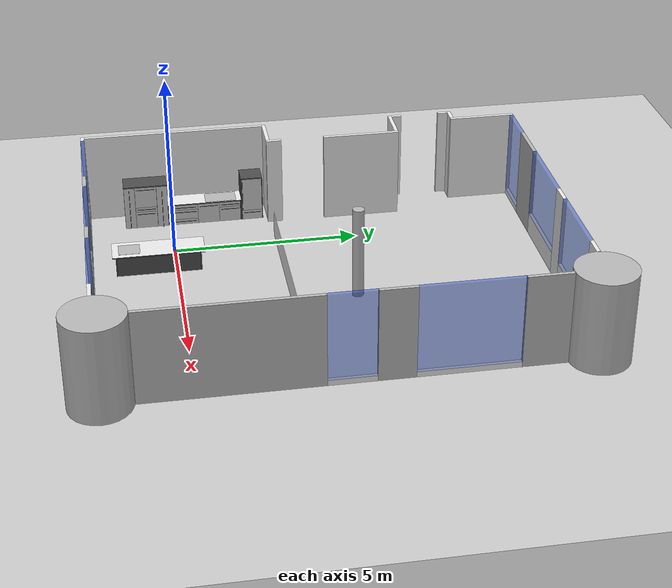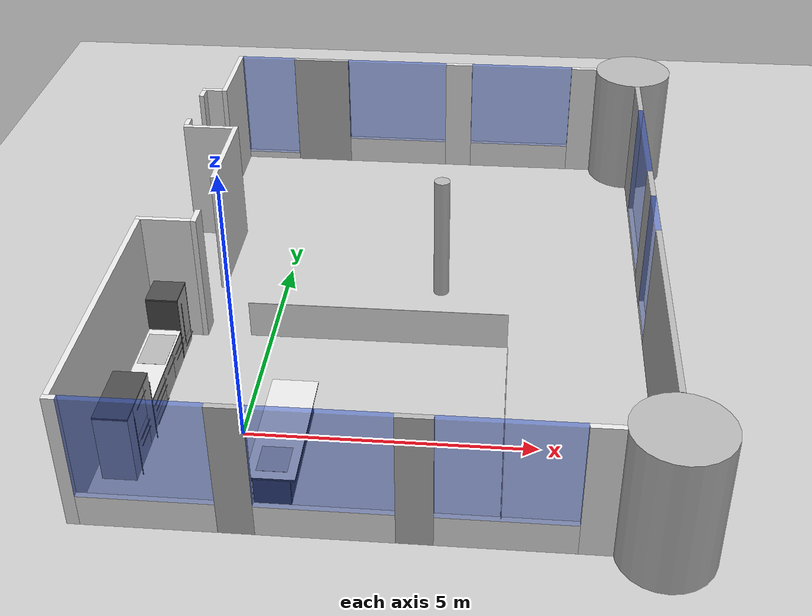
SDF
<sdf version="1.3">
 <world name="default">
  <light name="sun" type="directional">
   <pose>0.000000 0.000000 10.000000 0.000000 0.000000 0.000000</pose>
   <diffuse>0.800000 0.800000 0.800000 1.000000</diffuse>
   <specular>0.100000 0.100000 0.100000 1.000000</specular>
   <attenuation>
    <range>1000.000000</range>
    <constant>0.900000</constant>
    <linear>0.010000</linear>
    <quadratic>0.001000</quadratic>
   </attenuation>
   <direction>-0.500000 0.500000 -1.000000</direction>
  </light>
  <light name="sun_2" type="point">
   <pose>0.262421 0.000000 0.8201365 0.000000 0.000000 0.000000</pose>
   <diffuse>0.800000 0.800000 0.800000 1.000000</diffuse>
   <specular>0.100000 0.100000 0.100000 1.000000</specular>
   <attenuation>
    <range>1000.000000</range>
    <constant>0.900000</constant>
    <linear>0.010000</linear>
    <quadratic>0.001000</quadratic>
   </attenuation>
   <direction>-0.500000 0.500000 -1.000000</direction>
  </light>
  <model name="ground_plane">
   <static>1</static>
   <link name="link">
    <collision name="collision">
     <geometry>
      <plane><normal>0.000000 0.000000 1.000000</normal><size>100.000000 100.000000</size></plane>
     </geometry>
     <surface><friction><ode><mu>100.000000</mu><mu2>50.000000</mu2></ode></friction></surface>
    </collision>
    <visual name="visual">
     <cast_shadows>0</cast_shadows>
     <geometry>
      <plane><normal>0.000000 0.000000 1.000000</normal><size>100.000000 100.000000</size></plane>
     </geometry>
     <material>
      <script><uri>file://media/materials/scripts/gazebo.material</uri><name>Gazebo/Grey</name></script>
     </material>
    </visual>
    <velocity_decay><linear>0.000000</linear><angular>0.000000</angular></velocity_decay>
   </link>
  </model>
  <physics type="ode">
   <update_rate>1000.000000</update_rate>
   <gravity>0.000000 0.000000 -9.800000</gravity>
  </physics>
  <scene>
   <ambient>0.200000 0.200000 0.200000 1.000000</ambient>
   <background>0.700000 0.700000 0.700000 1.000000</background>
   <shadows>1</shadows>
  </scene>
  <model name="kitchen_description">
   <static>1</static>
   <pose>3.200000 5.600000 -0.250000 0.000000 0.000000 0.000000</pose>
   <link name="kitchen_link">
    <inertial>
     <pose>-4.141810 -5.062160 0.394622 0.000000 0.000000 0.000000</pose>
     <mass>91.300000</mass>
     <inertia>
      <ixx>2520.020000</ixx>
      <ixy>-1839.610000</ixy>
      <ixz>151.134000</ixz>
      <iyy>1740.550000</iyy>
      <iyz>179.109000</iyz>
      <izz>4177.000000</izz>
     </inertia>
    </inertial>
    <collision name="kitchen_link_geom_counter_bottom_fridge_link">
     <pose>-5.002500 -3.290000 0.515000 0.000000 0.000000 0.000000</pose>
     <geometry><box><size>0.575000 0.600000 0.030000</size></box></geometry>
     <surface>
      <contact><ode><kp>100000.000000</kp><kd>1000000.000000</kd></ode></contact>
      <friction><ode><mu>50000.000000</mu><mu2>50000.000000</mu2></ode></friction>
     </surface>
    </collision>
    <collision name="kitchen_link_geom_counter_middle_fridge_link">
     <pose>-5.077500 -3.290000 0.845000 0.000000 0.000000 0.000000</pose>
     <geometry><box><size>0.425000 0.600000 0.030000</size></box></geometry>
     <surface>
      <contact><ode><kp>100000.000000</kp><kd>1000000.000000</kd></ode></contact>
      <friction><ode><mu>50000.000000</mu><mu2>50000.000000</mu2></ode></friction>
     </surface>
    </collision>
    <collision name="kitchen_link_geom_counter_side_fridge_left_link">
     <pose>-5.000000 -3.580000 0.815000 0.000000 0.000000 0.000000</pose>
     <geometry><box><size>0.580000 0.020000 1.330000</size></box></geometry>
    </collision>
    <collision name="kitchen_link_geom_counter_side_fridge_right_link">
     <pose>-5.000000 -3.000000 0.815000 0.000000 0.000000 0.000000</pose>
     <geometry><box><size>0.580000 0.020000 1.330000</size></box></geometry>
    </collision>
    <collision name="kitchen_link_geom_counter_side_island_back_link">
     <pose>-2.110670 -6.069990 0.410000 0.000000 0.000000 3.141000</pose>
     <geometry><box><size>0.020000 2.200000 0.820000</size></box></geometry>
    </collision>
    <collision name="kitchen_link_geom_counter_side_island_left_link">
     <pose>-2.400010 -4.954820 0.410000 0.000000 0.000000 3.141000</pose>
     <geometry><box><size>0.600000 0.030000 0.820000</size></box></geometry>
    </collision>
    <collision name="kitchen_link_geom_counter_side_island_right_link">
     <pose>-2.401330 -7.184820 0.410000 0.000000 0.000000 3.141000</pose>
     <geometry><box><size>0.600000 0.030000 0.820000</size></box></geometry>
    </collision>
    <collision name="kitchen_link_geom_counter_side_sink_left_link">
     <pose>-5.000000 -5.635000 0.410000 0.000000 0.000000 0.000000</pose>
     <geometry><box><size>0.580000 0.030000 0.820000</size></box></geometry>
    </collision>
    <collision name="kitchen_link_geom_counter_side_sink_right_link">
     <pose>-5.000000 -3.605000 0.410000 0.000000 0.000000 0.000000</pose>
     <geometry><box><size>0.580000 0.030000 0.820000</size></box></geometry>
    </collision>
    <collision name="kitchen_link_geom_counter_top_fridge_link">
     <pose>-5.000000 -3.290000 1.495000 0.000000 0.000000 0.000000</pose>
     <geometry><box><size>0.580000 0.600000 0.030000</size></box></geometry>
     <surface>
      <contact><ode><kp>100000.000000</kp><kd>1000000.000000</kd></ode></contact>
      <friction><ode><mu>50000.000000</mu><mu2>50000.000000</mu2></ode></friction>
     </surface>
    </collision>
    <collision name="kitchen_link_geom_counter_top_island_link">
     <pose>-2.400670 -6.064820 0.835000 0.000000 0.000000 3.141000</pose>
     <geometry><box><size>0.800000 2.450000 0.030000</size></box></geometry>
     <surface>
      <contact><ode><kp>100000.000000</kp><kd>1000000.000000</kd></ode></contact>
      <friction><ode><mu>50000.000000</mu><mu2>50000.000000</mu2></ode></friction>
     </surface>
    </collision>
    <collision name="kitchen_link_geom_counter_top_oven_link">
     <pose>-4.980000 -6.250000 1.495000 0.000000 0.000000 0.000000</pose>
     <geometry><box><size>0.580000 1.200000 0.030000</size></box></geometry>
     <surface>
      <contact><ode><kp>100000.000000</kp><kd>1000000.000000</kd></ode></contact>
      <friction><ode><mu>50000.000000</mu><mu2>50000.000000</mu2></ode></friction>
     </surface>
    </collision>
    <collision name="kitchen_link_geom_counter_top_sink_link">
     <pose>-5.000000 -4.620000 0.835000 0.000000 0.000000 0.000000</pose>
     <geometry><box><size>0.580000 2.060000 0.030000</size></box></geometry>
     <surface>
      <contact><ode><kp>100000.000000</kp><kd>1000000.000000</kd></ode></contact>
      <friction><ode><mu>50000.000000</mu><mu2>50000.000000</mu2></ode></friction>
     </surface>
    </collision>
    <collision name="kitchen_link_geom_sink_link">
     <pose>-4.995000 -4.165000 0.852500 0.000000 0.000000 0.000000</pose>
     <geometry><box><size>0.500000 0.860000 0.005000</size></box></geometry>
    </collision>
    <collision name="kitchen_link_geom_skirting_fridge_link">
     <pose>-5.035000 -3.290000 0.075000 0.000000 0.000000 0.000000</pose>
     <geometry><box><size>0.510000 0.600000 0.150000</size></box></geometry>
    </collision>
    <collision name="kitchen_link_geom_skirting_island_link">
     <pose>-2.375670 -6.069840 0.050000 0.000000 0.000000 3.141000</pose>
     <geometry><box><size>0.510000 2.200000 0.100000</size></box></geometry>
    </collision>
    <collision name="kitchen_link_geom_skirting_oven_link">
     <pose>-5.015000 -6.250000 0.075000 0.000000 0.000000 0.000000</pose>
     <geometry><box><size>0.510000 1.200000 0.150000</size></box></geometry>
    </collision>
    <collision name="kitchen_link_geom_skirting_sink_link">
     <pose>-5.035000 -4.620000 0.050000 0.000000 0.000000 0.000000</pose>
     <geometry><box><size>0.510000 2.000000 0.100000</size></box></geometry>
    </collision>
    <collision name="kitchen_link_geom_stove_link">
     <pose>-2.401120 -6.834820 0.852500 0.000000 0.000000 3.141000</pose>
     <geometry><box><size>0.500000 0.570000 0.005000</size></box></geometry>
    </collision>
    <collision name="kitchen_link_geom_white_counter_top_island_link">
     <pose>-2.400670 -6.064820 0.851000 0.000000 0.000000 3.141000</pose>
     <geometry><box><size>0.800000 2.450000 0.002000</size></box></geometry>
     <surface>
      <contact><ode><kp>100000.000000</kp><kd>1000000.000000</kd></ode></contact>
      <friction><ode><mu>50000.000000</mu><mu2>50000.000000</mu2></ode></friction>
     </surface>
    </collision>
    <collision name="kitchen_link_geom_white_counter_top_sink_link">
     <pose>-5.000000 -4.620000 0.851000 0.000000 0.000000 0.000000</pose>
     <geometry><box><size>0.580000 2.060000 0.002000</size></box></geometry>
     <surface>
      <contact><ode><kp>100000.000000</kp><kd>1000000.000000</kd></ode></contact>
      <friction><ode><mu>50000.000000</mu><mu2>50000.000000</mu2></ode></friction>
     </surface>
    </collision>
    <visual name="kitchen_link_visualcounter_bottom_fridge_link">
     <pose>-5.002500 -3.290000 0.515000 0.000000 0.000000 0.000000</pose>
     <geometry><box><size>0.575000 0.600000 0.030000</size></box></geometry>
     <material>
      <script>
       <name>Ias/KitchenWhite</name>
       <uri>model://lab/materials/scripts</uri>
       <uri>model://lab/materials/textures</uri>
      </script>
     </material>
    </visual>
    <visual name="kitchen_link_visualcounter_middle_fridge_link">
     <pose>-5.077500 -3.290000 0.845000 0.000000 0.000000 0.000000</pose>
     <geometry><box><size>0.425000 0.600000 0.030000</size></box></geometry>
     <material>
      <script>
       <name>Ias/KitchenWhite</name>
       <uri>model://lab/materials/scripts</uri>
       <uri>model://lab/materials/textures</uri>
      </script>
     </material>
    </visual>
    <visual name="kitchen_link_visualcounter_side_fridge_left_link">
     <pose>-5.000000 -3.580000 0.815000 0.000000 0.000000 0.000000</pose>
     <geometry><box><size>0.580000 0.020000 1.330000</size></box></geometry>
     <material>
      <script>
       <name>Ias/KitchenDarkGray</name>
       <uri>model://lab/materials/scripts</uri>
       <uri>model://lab/materials/textures</uri>
      </script>
     </material>
    </visual>
    <visual name="kitchen_link_visualcounter_side_fridge_right_link">
     <pose>-5.000000 -3.000000 0.815000 0.000000 0.000000 0.000000</pose>
     <geometry><box><size>0.580000 0.020000 1.330000</size></box></geometry>
     <material>
      <script>
       <name>Ias/KitchenDarkGray</name>
       <uri>model://lab/materials/scripts</uri>
       <uri>model://lab/materials/textures</uri>
      </script>
     </material>
    </visual>
    <visual name="kitchen_link_visualcounter_side_island_back_link">
     <pose>-2.110670 -6.069990 0.410000 0.000000 0.000000 3.141000</pose>
     <geometry><box><size>0.020000 2.200000 0.820000</size></box></geometry>
     <material>
      <script>
       <name>Ias/KitchenDarkGray</name>
       <uri>model://lab/materials/scripts</uri>
       <uri>model://lab/materials/textures</uri>
      </script>
     </material>
    </visual>
    <visual name="kitchen_link_visualcounter_side_island_left_link">
     <pose>-2.400010 -4.954820 0.410000 0.000000 0.000000 3.141000</pose>
     <geometry><box><size>0.600000 0.030000 0.820000</size></box></geometry>
     <material>
      <script>
       <name>Ias/KitchenDarkGray</name>
       <uri>model://lab/materials/scripts</uri>
       <uri>model://lab/materials/textures</uri>
      </script>
     </material>
    </visual>
    <visual name="kitchen_link_visualcounter_side_island_right_link">
     <pose>-2.401330 -7.184820 0.410000 0.000000 0.000000 3.141000</pose>
     <geometry><box><size>0.600000 0.030000 0.820000</size></box></geometry>
     <material>
      <script>
       <name>Ias/KitchenDarkGray</name>
       <uri>model://lab/materials/scripts</uri>
       <uri>model://lab/materials/textures</uri>
      </script>
     </material>
    </visual>
    <visual name="kitchen_link_visualcounter_side_sink_left_link">
     <pose>-5.000000 -5.635000 0.410000 0.000000 0.000000 0.000000</pose>
     <geometry><box><size>0.580000 0.030000 0.820000</size></box></geometry>
     <material>
      <script>
       <name>Ias/KitchenDarkGray</name>
       <uri>model://lab/materials/scripts</uri>
       <uri>model://lab/materials/textures</uri>
      </script>
     </material>
    </visual>
    <visual name="kitchen_link_visualcounter_side_sink_right_link">
     <pose>-5.000000 -3.605000 0.410000 0.000000 0.000000 0.000000</pose>
     <geometry><box><size>0.580000 0.030000 0.820000</size></box></geometry>
     <material>
      <script>
       <name>Ias/KitchenDarkGray</name>
       <uri>model://lab/materials/scripts</uri>
       <uri>model://lab/materials/textures</uri>
      </script>
     </material>
    </visual>
    <visual name="kitchen_link_visualcounter_top_fridge_link">
     <pose>-5.000000 -3.290000 1.495000 0.000000 0.000000 0.000000</pose>
     <geometry><box><size>0.580000 0.600000 0.030000</size></box></geometry>
     <material>
      <script>
       <name>Ias/KitchenDarkGray</name>
       <uri>model://lab/materials/scripts</uri>
       <uri>model://lab/materials/textures</uri>
      </script>
     </material>
    </visual>
    <visual name="kitchen_link_visualcounter_top_island_link">
     <pose>-2.400670 -6.064820 0.835000 0.000000 0.000000 3.141000</pose>
     <geometry><box><size>0.800000 2.450000 0.030000</size></box></geometry>
     <material>
      <script>
       <name>Ias/KitchenDarkGray</name>
       <uri>model://lab/materials/scripts</uri>
       <uri>model://lab/materials/textures</uri>
      </script>
     </material>
    </visual>
    <visual name="kitchen_link_visualcounter_top_oven_link">
     <pose>-4.980000 -6.250000 1.495000 0.000000 0.000000 0.000000</pose>
     <geometry><box><size>0.580000 1.200000 0.030000</size></box></geometry>
     <material>
      <script>
       <name>Ias/KitchenDarkGray</name>
       <uri>model://lab/materials/scripts</uri>
       <uri>model://lab/materials/textures</uri>
      </script>
     </material>
    </visual>
    <visual name="kitchen_link_visualcounter_top_sink_link">
     <pose>-5.000000 -4.620000 0.835000 0.000000 0.000000 0.000000</pose>
     <geometry><box><size>0.580000 2.060000 0.030000</size></box></geometry>
     <material>
      <script>
       <name>Ias/KitchenDarkGray</name>
       <uri>model://lab/materials/scripts</uri>
       <uri>model://lab/materials/textures</uri>
      </script>
     </material>
    </visual>
    <visual name="kitchen_link_visualfridge_block_link">
     <pose>-5.290000 -3.590000 0.000000 0.000000 0.000000 0.000000</pose>
     <geometry><box><size>0.100000 0.100000 0.100000</size></box></geometry>
    </visual>
    <visual name="kitchen_link_visualisland_block_link">
     <pose>-2.100000 -4.940000 0.000000 0.000000 0.000000 3.141000</pose>
     <geometry><box><size>0.100000 0.100000 0.100000</size></box></geometry>
    </visual>
    <visual name="kitchen_link_visualoven_block_link">
     <pose>-5.270000 -6.850000 0.000000 0.000000 0.000000 0.000000</pose>
     <geometry><box><size>0.100000 0.100000 0.100000</size></box></geometry>
    </visual>
    <visual name="kitchen_link_visualsink_block_link">
     <pose>-5.290000 -5.650000 0.000000 0.000000 0.000000 0.000000</pose>
     <geometry><box><size>0.100000 0.100000 0.100000</size></box></geometry>
    </visual>
    <visual name="kitchen_link_visualsink_link">
     <pose>-4.995000 -4.165000 0.852500 0.000000 0.000000 0.000000</pose>
     <geometry><box><size>0.500000 0.860000 0.005000</size></box></geometry>
     <material>
      <script>
       <name>Ias/KitchenSink</name>
       <uri>model://lab/materials/scripts</uri>
       <uri>model://lab/materials/textures</uri>
      </script>
     </material>
    </visual>
    <visual name="kitchen_link_visualskirting_fridge_link">
     <pose>-5.035000 -3.290000 0.075000 0.000000 0.000000 0.000000</pose>
     <geometry><box><size>0.510000 0.600000 0.150000</size></box></geometry>
     <material>
      <script>
       <name>Ias/KitchenDarkGray</name>
       <uri>model://lab/materials/scripts</uri>
       <uri>model://lab/materials/textures</uri>
      </script>
     </material>
    </visual>
    <visual name="kitchen_link_visualskirting_island_link">
     <pose>-2.375670 -6.069840 0.050000 0.000000 0.000000 3.141000</pose>
     <geometry><box><size>0.510000 2.200000 0.100000</size></box></geometry>
     <material>
      <script>
       <name>Ias/KitchenDarkGray</name>
       <uri>model://lab/materials/scripts</uri>
       <uri>model://lab/materials/textures</uri>
      </script>
     </material>
    </visual>
    <visual name="kitchen_link_visualskirting_oven_link">
     <pose>-5.015000 -6.250000 0.075000 0.000000 0.000000 0.000000</pose>
     <geometry><box><size>0.510000 1.200000 0.150000</size></box></geometry>
     <material>
      <script>
       <name>Ias/KitchenDarkGray</name>
       <uri>model://lab/materials/scripts</uri>
       <uri>model://lab/materials/textures</uri>
      </script>
     </material>
    </visual>
    <visual name="kitchen_link_visualskirting_sink_link">
     <pose>-5.035000 -4.620000 0.050000 0.000000 0.000000 0.000000</pose>
     <geometry><box><size>0.510000 2.000000 0.100000</size></box></geometry>
     <material>
      <script>
       <name>Ias/KitchenDarkGray</name>
       <uri>model://lab/materials/scripts</uri>
       <uri>model://lab/materials/textures</uri>
      </script>
     </material>
    </visual>
    <visual name="kitchen_link_visualstove_link">
     <pose>-2.401120 -6.834820 0.852500 0.000000 0.000000 3.141000</pose>
     <geometry><box><size>0.500000 0.570000 0.005000</size></box></geometry>
     <material>
      <script>
       <name>Ias/KitchenStove</name>
       <uri>model://lab/materials/scripts</uri>
       <uri>model://lab/materials/textures</uri>
      </script>
     </material>
    </visual>
    <visual name="kitchen_link_visualwhite_counter_top_island_link">
     <pose>-2.400670 -6.064820 0.851000 0.000000 0.000000 3.141000</pose>
     <geometry><box><size>0.800000 2.450000 0.002000</size></box></geometry>
     <material>
      <script>
       <name>Ias/KitchenWhite</name>
       <uri>model://lab/materials/scripts</uri>
       <uri>model://lab/materials/textures</uri>
      </script>
     </material>
    </visual>
    <visual name="kitchen_link_visualwhite_counter_top_sink_link">
     <pose>-5.000000 -4.620000 0.851000 0.000000 0.000000 0.000000</pose>
     <geometry><box><size>0.580000 2.060000 0.002000</size></box></geometry>
     <material>
      <script>
       <name>Ias/KitchenWhite</name>
       <uri>model://lab/materials/scripts</uri>
       <uri>model://lab/materials/textures</uri>
      </script>
     </material>
    </visual>
    <velocity_decay><linear>0.000000</linear><angular>0.000000</angular></velocity_decay>
    <velocity_decay><linear>0.000000</linear><angular>0.000000</angular></velocity_decay>
    <velocity_decay><linear>0.000000</linear><angular>0.000000</angular></velocity_decay>
    <velocity_decay><linear>0.000000</linear><angular>0.000000</angular></velocity_decay>
    <velocity_decay><linear>0.000000</linear><angular>0.000000</angular></velocity_decay>
    <velocity_decay><linear>0.000000</linear><angular>0.000000</angular></velocity_decay>
    <velocity_decay><linear>0.000000</linear><angular>0.000000</angular></velocity_decay>
    <velocity_decay><linear>0.000000</linear><angular>0.000000</angular></velocity_decay>
    <velocity_decay><linear>0.000000</linear><angular>0.000000</angular></velocity_decay>
    <velocity_decay><linear>0.000000</linear><angular>0.000000</angular></velocity_decay>
    <velocity_decay><linear>0.000000</linear><angular>0.000000</angular></velocity_decay>
    <velocity_decay><linear>0.000000</linear><angular>0.000000</angular></velocity_decay>
    <velocity_decay><linear>0.000000</linear><angular>0.000000</angular></velocity_decay>
    <velocity_decay><linear>0.000000</linear><angular>0.000000</angular></velocity_decay>
    <velocity_decay><linear>0.000000</linear><angular>0.000000</angular></velocity_decay>
    <velocity_decay><linear>0.000000</linear><angular>0.000000</angular></velocity_decay>
    <velocity_decay><linear>0.000000</linear><angular>0.000000</angular></velocity_decay>
    <velocity_decay><linear>0.000000</linear><angular>0.000000</angular></velocity_decay>
    <velocity_decay><linear>0.000000</linear><angular>0.000000</angular></velocity_decay>
    <velocity_decay><linear>0.000000</linear><angular>0.000000</angular></velocity_decay>
    <velocity_decay><linear>0.000000</linear><angular>0.000000</angular></velocity_decay>
   </link>
   <link name="drawer_fridge_bottom_link">
    <pose>-4.720000 -3.290000 0.332500 0.000000 0.000000 0.000000</pose>
    <inertial>
     <pose>0.001225 0.000000 0.002549 0.000000 0.000000 0.000000</pose>
     <mass>5.100000</mass>
     <inertia>
      <ixx>0.102180</ixx>
      <ixy>0.000000</ixy>
      <ixz>-0.000812</ixz>
      <iyy>0.139595</iyy>
      <iyz>0.000000</iyz>
      <izz>0.109301</izz>
     </inertia>
    </inertial>
    <collision name="drawer_fridge_bottom_link_geom">
     <geometry><box><size>0.020000 0.565000 0.365000</size></box></geometry>
    </collision>
    <collision name="drawer_fridge_bottom_link_geom_drawer_fridge_bottom_back_link">
     <pose>-0.540000 0.000000 0.000000 0.000000 0.000000 0.000000</pose>
     <geometry><box><size>0.020000 0.465000 0.315000</size></box></geometry>
    </collision>
    <collision name="drawer_fridge_bottom_link_geom_drawer_fridge_bottom_bottom_link">
     <pose>-0.270000 0.000000 -0.147500 0.000000 0.000000 0.000000</pose>
     <geometry><box><size>0.540000 0.465000 0.020000</size></box></geometry>
    </collision>
    <collision name="drawer_fridge_bottom_link_geom_drawer_fridge_bottom_left_link">
     <pose>-0.270000 -0.222500 0.000000 0.000000 0.000000 0.000000</pose>
     <geometry><box><size>0.540000 0.020000 0.315000</size></box></geometry>
    </collision>
    <collision name="drawer_fridge_bottom_link_geom_drawer_fridge_bottom_right_link">
     <pose>-0.270000 0.222500 0.000000 0.000000 0.000000 0.000000</pose>
     <geometry><box><size>0.540000 0.020000 0.315000</size></box></geometry>
    </collision>
    <collision name="drawer_fridge_bottom_link_geom_handle_drawer_fridge_bottom_link">
     <pose>0.062500 0.000000 0.130000 0.000000 0.000000 0.000000</pose>
     <geometry><box><size>0.015000 0.475000 0.015000</size></box></geometry>
    </collision>
    <visual name="drawer_fridge_bottom_link_visual">
     <geometry><box><size>0.020000 0.560000 0.360000</size></box></geometry>
     <material>
      <script>
       <name>Ias/KitchenLightGray</name>
       <uri>model://lab/materials/scripts</uri>
       <uri>model://lab/materials/textures</uri>
      </script>
     </material>
    </visual>
    <visual name="drawer_fridge_bottom_link_visualdrawer_fridge_bottom_back_link">
     <pose>-0.540000 0.000000 0.000000 0.000000 0.000000 0.000000</pose>
     <geometry><box><size>0.020000 0.465000 0.315000</size></box></geometry>
     <material>
      <script>
       <name>Ias/KitchenLightGray</name>
       <uri>model://lab/materials/scripts</uri>
       <uri>model://lab/materials/textures</uri>
      </script>
     </material>
    </visual>
    <visual name="drawer_fridge_bottom_link_visualdrawer_fridge_bottom_bottom_link">
     <pose>-0.270000 0.000000 -0.147500 0.000000 0.000000 0.000000</pose>
     <geometry><box><size>0.540000 0.465000 0.020000</size></box></geometry>
     <material>
      <script>
       <name>Ias/KitchenLightGray</name>
       <uri>model://lab/materials/scripts</uri>
       <uri>model://lab/materials/textures</uri>
      </script>
     </material>
    </visual>
    <visual name="drawer_fridge_bottom_link_visualdrawer_fridge_bottom_left_link">
     <pose>-0.270000 -0.222500 0.000000 0.000000 0.000000 0.000000</pose>
     <geometry><box><size>0.540000 0.020000 0.315000</size></box></geometry>
     <material>
      <script>
       <name>Ias/KitchenLightGray</name>
       <uri>model://lab/materials/scripts</uri>
       <uri>model://lab/materials/textures</uri>
      </script>
     </material>
    </visual>
    <visual name="drawer_fridge_bottom_link_visualdrawer_fridge_bottom_right_link">
     <pose>-0.270000 0.222500 0.000000 0.000000 0.000000 0.000000</pose>
     <geometry><box><size>0.540000 0.020000 0.315000</size></box></geometry>
     <material>
      <script>
       <name>Ias/KitchenLightGray</name>
       <uri>model://lab/materials/scripts</uri>
       <uri>model://lab/materials/textures</uri>
      </script>
     </material>
    </visual>
    <visual name="drawer_fridge_bottom_link_visualhandle_drawer_fridge_bottom_link">
     <pose>0.062500 0.000000 0.130000 0.000000 0.000000 0.000000</pose>
     <geometry><box><size>0.010000 0.470000 0.010000</size></box></geometry>
     <material>
      <script>
       <name>Ias/KitchenDarkGray</name>
       <uri>model://lab/materials/scripts</uri>
       <uri>model://lab/materials/textures</uri>
      </script>
     </material>
    </visual>
    <velocity_decay><linear>0.000000</linear><angular>0.000000</angular></velocity_decay>
    <velocity_decay><linear>0.000000</linear><angular>0.000000</angular></velocity_decay>
    <velocity_decay><linear>0.000000</linear><angular>0.000000</angular></velocity_decay>
    <velocity_decay><linear>0.000000</linear><angular>0.000000</angular></velocity_decay>
    <velocity_decay><linear>0.000000</linear><angular>0.000000</angular></velocity_decay>
    <velocity_decay><linear>0.000000</linear><angular>0.000000</angular></velocity_decay>
   </link>
   <joint name="fridge_block_drawer_fridge_bottom_joint" type="prismatic">
    <child>drawer_fridge_bottom_link</child>
    <parent>kitchen_link</parent>
    <axis>
     <xyz>0.999000 0.000000 0.044000</xyz>
     <limit>
      <lower>0.000000</lower>
      <upper>0.480000</upper>
      <effort>300.000000</effort>
      <velocity>10.000000</velocity>
     </limit>
    </axis>
    <physics>
     <ode>
      <provide_feedback>0</provide_feedback>
      <cfm_damping>0</cfm_damping>
      <limit><cfm>0.000000</cfm><erp>0.200000</erp></limit>
     </ode>
    </physics>
   </joint>
   <link name="fridge_link">
    <pose>-4.710000 -2.990000 0.995000 0.000000 0.000000 0.000000</pose>
    <inertial>
     <pose>0.005682 -0.051818 0.000000 0.000000 0.000000 0.000000</pose>
     <mass>1.100000</mass>
     <inertia>
      <ixx>0.145975</ixx>
      <ixy>0.003563</ixy>
      <ixz>0.000000</ixz>
      <iyy>0.029896</iyy>
      <iyz>0.000000</iyz>
      <izz>0.116866</izz>
     </inertia>
    </inertial>
    <collision name="fridge_link_geom">
     <pose>-0.005000 -0.300000 0.000000 0.000000 0.000000 0.000000</pose>
     <geometry><box><size>0.010000 0.600000 0.970000</size></box></geometry>
    </collision>
    <collision name="fridge_link_geom_handle_fridge_link">
     <pose>0.062500 -0.570000 0.000000 0.000000 0.000000 0.000000</pose>
     <geometry><box><size>0.015000 0.015000 0.880000</size></box></geometry>
    </collision>
    <visual name="fridge_link_visual">
     <pose>-0.005000 -0.300000 0.000000 0.000000 0.000000 0.000000</pose>
     <geometry><box><size>0.005000 0.595000 0.965000</size></box></geometry>
     <material>
      <script>
       <name>Ias/KitchenLightGray</name>
       <uri>model://lab/materials/scripts</uri>
       <uri>model://lab/materials/textures</uri>
      </script>
     </material>
    </visual>
    <visual name="fridge_link_visualhandle_fridge_link">
     <pose>0.062500 -0.570000 0.000000 0.000000 0.000000 0.000000</pose>
     <geometry><box><size>0.010000 0.010000 0.875000</size></box></geometry>
     <material>
      <script>
       <name>Ias/KitchenDarkGray</name>
       <uri>model://lab/materials/scripts</uri>
       <uri>model://lab/materials/textures</uri>
      </script>
     </material>
    </visual>
    <velocity_decay><linear>0.000000</linear><angular>0.000000</angular></velocity_decay>
    <velocity_decay><linear>0.000000</linear><angular>0.000000</angular></velocity_decay>
   </link>
   <joint name="fridge_block_fridge_joint" type="revolute">
    <child>fridge_link</child>
    <parent>kitchen_link</parent>
    <axis>
     <xyz>0.000000 0.000000 1.000000</xyz>
     <limit>
      <lower>0.000000</lower>
      <upper>1.300000</upper>
      <effort>300.000000</effort>
      <velocity>10.000000</velocity>
     </limit>
    </axis>
   </joint>
   <link name="drawer_island_col1_bottom_link">
    <pose>-2.670200 -5.269660 0.245000 0.000000 0.000000 3.141000</pose>
    <inertial>
     <pose>0.001225 0.000000 0.001814 0.000000 0.000000 0.000000</pose>
     <mass>5.100000</mass>
     <inertia>
      <ixx>0.096157</ixx>
      <ixy>0.000000</ixy>
      <ixz>-0.000578</ixz>
      <iyy>0.148072</iyy>
      <iyz>0.000000</iyz>
      <izz>0.094801</izz>
     </inertia>
    </inertial>
    <collision name="drawer_island_col1_bottom_link_geom">
     <geometry><box><size>0.020000 0.600000 0.290000</size></box></geometry>
    </collision>
    <collision name="drawer_island_col1_bottom_link_geom_drawer_island_col1_bottom_back_link">
     <pose>-0.540000 0.000000 0.000000 0.000000 0.000000 0.000000</pose>
     <geometry><box><size>0.020000 0.500000 0.240000</size></box></geometry>
    </collision>
    <collision name="drawer_island_col1_bottom_link_geom_drawer_island_col1_bottom_bottom_link">
     <pose>-0.270000 0.000000 -0.110000 0.000000 0.000000 0.000000</pose>
     <geometry><box><size>0.540000 0.500000 0.020000</size></box></geometry>
    </collision>
    <collision name="drawer_island_col1_bottom_link_geom_drawer_island_col1_bottom_left_link">
     <pose>-0.270000 -0.240000 0.000000 0.000000 0.000000 0.000000</pose>
     <geometry><box><size>0.540000 0.020000 0.240000</size></box></geometry>
    </collision>
    <collision name="drawer_island_col1_bottom_link_geom_drawer_island_col1_bottom_right_link">
     <pose>-0.270000 0.240000 0.000000 0.000000 0.000000 0.000000</pose>
     <geometry><box><size>0.540000 0.020000 0.240000</size></box></geometry>
    </collision>
    <collision name="drawer_island_col1_bottom_link_geom_handle_drawer_island_col1_bottom_link">
     <pose>0.062500 0.000000 0.092500 0.000000 0.000000 0.000000</pose>
     <geometry><box><size>0.015000 0.510000 0.015000</size></box></geometry>
    </collision>
    <visual name="drawer_island_col1_bottom_link_visual">
     <geometry><box><size>0.020000 0.595000 0.285000</size></box></geometry>
     <material>
      <script>
       <name>Ias/KitchenLightGray</name>
       <uri>model://lab/materials/scripts</uri>
       <uri>model://lab/materials/textures</uri>
      </script>
     </material>
    </visual>
    <visual name="drawer_island_col1_bottom_link_visualdrawer_island_col1_bottom_back_link">
     <pose>-0.540000 0.000000 0.000000 0.000000 0.000000 0.000000</pose>
     <geometry><box><size>0.020000 0.500000 0.240000</size></box></geometry>
     <material>
      <script>
       <name>Ias/KitchenLightGray</name>
       <uri>model://lab/materials/scripts</uri>
       <uri>model://lab/materials/textures</uri>
      </script>
     </material>
    </visual>
    <visual name="drawer_island_col1_bottom_link_visualdrawer_island_col1_bottom_bottom_link">
     <pose>-0.270000 0.000000 -0.110000 0.000000 0.000000 0.000000</pose>
     <geometry><box><size>0.540000 0.500000 0.020000</size></box></geometry>
     <material>
      <script>
       <name>Ias/KitchenLightGray</name>
       <uri>model://lab/materials/scripts</uri>
       <uri>model://lab/materials/textures</uri>
      </script>
     </material>
    </visual>
    <visual name="drawer_island_col1_bottom_link_visualdrawer_island_col1_bottom_left_link">
     <pose>-0.270000 -0.240000 0.000000 0.000000 0.000000 0.000000</pose>
     <geometry><box><size>0.540000 0.020000 0.240000</size></box></geometry>
     <material>
      <script>
       <name>Ias/KitchenLightGray</name>
       <uri>model://lab/materials/scripts</uri>
       <uri>model://lab/materials/textures</uri>
      </script>
     </material>
    </visual>
    <visual name="drawer_island_col1_bottom_link_visualdrawer_island_col1_bottom_right_link">
     <pose>-0.270000 0.240000 0.000000 0.000000 0.000000 0.000000</pose>
     <geometry><box><size>0.540000 0.020000 0.240000</size></box></geometry>
     <material>
      <script>
       <name>Ias/KitchenLightGray</name>
       <uri>model://lab/materials/scripts</uri>
       <uri>model://lab/materials/textures</uri>
      </script>
     </material>
    </visual>
    <visual name="drawer_island_col1_bottom_link_visualhandle_drawer_island_col1_bottom_link">
     <pose>0.062500 0.000000 0.092500 0.000000 0.000000 0.000000</pose>
     <geometry><box><size>0.010000 0.505000 0.010000</size></box></geometry>
     <material>
      <script>
       <name>Ias/KitchenDarkGray</name>
       <uri>model://lab/materials/scripts</uri>
       <uri>model://lab/materials/textures</uri>
      </script>
     </material>
    </visual>
    <velocity_decay><linear>0.000000</linear><angular>0.000000</angular></velocity_decay>
    <velocity_decay><linear>0.000000</linear><angular>0.000000</angular></velocity_decay>
    <velocity_decay><linear>0.000000</linear><angular>0.000000</angular></velocity_decay>
    <velocity_decay><linear>0.000000</linear><angular>0.000000</angular></velocity_decay>
    <velocity_decay><linear>0.000000</linear><angular>0.000000</angular></velocity_decay>
    <velocity_decay><linear>0.000000</linear><angular>0.000000</angular></velocity_decay>
   </link>
   <joint name="island_block_drawer_island_col1_bottom_joint" type="prismatic">
    <child>drawer_island_col1_bottom_link</child>
    <parent>kitchen_link</parent>
    <axis>
     <xyz>-0.999000 0.000592 0.044000</xyz>
     <limit>
      <lower>0.000000</lower>
      <upper>0.480000</upper>
      <effort>300.000000</effort>
      <velocity>10.000000</velocity>
     </limit>
    </axis>
    <physics>
     <ode>
      <provide_feedback>0</provide_feedback>
      <cfm_damping>0</cfm_damping>
      <limit><cfm>0.000000</cfm><erp>0.200000</erp></limit>
     </ode>
    </physics>
   </joint>
   <link name="drawer_island_col1_center_link">
    <pose>-2.670200 -5.269660 0.535000 0.000000 0.000000 3.141000</pose>
    <inertial>
     <pose>0.001225 0.000000 0.001814 0.000000 0.000000 0.000000</pose>
     <mass>5.100000</mass>
     <inertia>
      <ixx>0.096157</ixx>
      <ixy>0.000000</ixy>
      <ixz>-0.000578</ixz>
      <iyy>0.148072</iyy>
      <iyz>0.000000</iyz>
      <izz>0.094801</izz>
     </inertia>
    </inertial>
    <collision name="drawer_island_col1_center_link_geom">
     <geometry><box><size>0.020000 0.600000 0.290000</size></box></geometry>
    </collision>
    <collision name="drawer_island_col1_center_link_geom_drawer_island_col1_center_back_link">
     <pose>-0.540000 0.000000 0.000000 0.000000 0.000000 0.000000</pose>
     <geometry><box><size>0.020000 0.500000 0.240000</size></box></geometry>
    </collision>
    <collision name="drawer_island_col1_center_link_geom_drawer_island_col1_center_bottom_link">
     <pose>-0.270000 0.000000 -0.110000 0.000000 0.000000 0.000000</pose>
     <geometry><box><size>0.540000 0.500000 0.020000</size></box></geometry>
    </collision>
    <collision name="drawer_island_col1_center_link_geom_drawer_island_col1_center_left_link">
     <pose>-0.270000 -0.240000 0.000000 0.000000 0.000000 0.000000</pose>
     <geometry><box><size>0.540000 0.020000 0.240000</size></box></geometry>
    </collision>
    <collision name="drawer_island_col1_center_link_geom_drawer_island_col1_center_right_link">
     <pose>-0.270000 0.240000 0.000000 0.000000 0.000000 0.000000</pose>
     <geometry><box><size>0.540000 0.020000 0.240000</size></box></geometry>
    </collision>
    <collision name="drawer_island_col1_center_link_geom_handle_drawer_island_col1_center_link">
     <pose>0.062500 0.000000 0.092500 0.000000 0.000000 0.000000</pose>
     <geometry><box><size>0.015000 0.510000 0.015000</size></box></geometry>
    </collision>
    <visual name="drawer_island_col1_center_link_visual">
     <geometry><box><size>0.020000 0.595000 0.285000</size></box></geometry>
     <material>
      <script>
       <name>Ias/KitchenLightGray</name>
       <uri>model://lab/materials/scripts</uri>
       <uri>model://lab/materials/textures</uri>
      </script>
     </material>
    </visual>
    <visual name="drawer_island_col1_center_link_visualdrawer_island_col1_center_back_link">
     <pose>-0.540000 0.000000 0.000000 0.000000 0.000000 0.000000</pose>
     <geometry><box><size>0.020000 0.500000 0.240000</size></box></geometry>
     <material>
      <script>
       <name>Ias/KitchenLightGray</name>
       <uri>model://lab/materials/scripts</uri>
       <uri>model://lab/materials/textures</uri>
      </script>
     </material>
    </visual>
    <visual name="drawer_island_col1_center_link_visualdrawer_island_col1_center_bottom_link">
     <pose>-0.270000 0.000000 -0.110000 0.000000 0.000000 0.000000</pose>
     <geometry><box><size>0.540000 0.500000 0.020000</size></box></geometry>
     <material>
      <script>
       <name>Ias/KitchenLightGray</name>
       <uri>model://lab/materials/scripts</uri>
       <uri>model://lab/materials/textures</uri>
      </script>
     </material>
    </visual>
    <visual name="drawer_island_col1_center_link_visualdrawer_island_col1_center_left_link">
     <pose>-0.270000 -0.240000 0.000000 0.000000 0.000000 0.000000</pose>
     <geometry><box><size>0.540000 0.020000 0.240000</size></box></geometry>
     <material>
      <script>
       <name>Ias/KitchenLightGray</name>
       <uri>model://lab/materials/scripts</uri>
       <uri>model://lab/materials/textures</uri>
      </script>
     </material>
    </visual>
    <visual name="drawer_island_col1_center_link_visualdrawer_island_col1_center_right_link">
     <pose>-0.270000 0.240000 0.000000 0.000000 0.000000 0.000000</pose>
     <geometry><box><size>0.540000 0.020000 0.240000</size></box></geometry>
     <material>
      <script>
       <name>Ias/KitchenLightGray</name>
       <uri>model://lab/materials/scripts</uri>
       <uri>model://lab/materials/textures</uri>
      </script>
     </material>
    </visual>
    <visual name="drawer_island_col1_center_link_visualhandle_drawer_island_col1_center_link">
     <pose>0.062500 0.000000 0.092500 0.000000 0.000000 0.000000</pose>
     <geometry><box><size>0.010000 0.505000 0.010000</size></box></geometry>
     <material>
      <script>
       <name>Ias/KitchenDarkGray</name>
       <uri>model://lab/materials/scripts</uri>
       <uri>model://lab/materials/textures</uri>
      </script>
     </material>
    </visual>
    <velocity_decay><linear>0.000000</linear><angular>0.000000</angular></velocity_decay>
    <velocity_decay><linear>0.000000</linear><angular>0.000000</angular></velocity_decay>
    <velocity_decay><linear>0.000000</linear><angular>0.000000</angular></velocity_decay>
    <velocity_decay><linear>0.000000</linear><angular>0.000000</angular></velocity_decay>
    <velocity_decay><linear>0.000000</linear><angular>0.000000</angular></velocity_decay>
    <velocity_decay><linear>0.000000</linear><angular>0.000000</angular></velocity_decay>
   </link>
   <joint name="island_block_drawer_island_col1_center_joint" type="prismatic">
    <child>drawer_island_col1_center_link</child>
    <parent>kitchen_link</parent>
    <axis>
     <xyz>-0.999000 0.000592 0.044000</xyz>
     <limit>
      <lower>0.000000</lower>
      <upper>0.480000</upper>
      <effort>300.000000</effort>
      <velocity>10.000000</velocity>
     </limit>
    </axis>
    <physics>
     <ode>
      <provide_feedback>0</provide_feedback>
      <cfm_damping>0</cfm_damping>
      <limit><cfm>0.000000</cfm><erp>0.200000</erp></limit>
     </ode>
    </physics>
   </joint>
   <link name="drawer_island_col1_top_link">
    <pose>-2.670200 -5.269660 0.750000 0.000000 0.000000 3.141000</pose>
    <inertial>
     <pose>0.001225 0.000000 0.000343 0.000000 0.000000 0.000000</pose>
     <mass>5.100000</mass>
     <inertia>
      <ixx>0.077582</ixx>
      <ixy>0.000000</ixy>
      <ixz>-0.000109</ixz>
      <iyy>0.147247</iyy>
      <iyz>0.000000</iyz>
      <izz>0.077051</izz>
     </inertia>
    </inertial>
    <collision name="drawer_island_col1_top_link_geom">
     <geometry><box><size>0.020000 0.600000 0.140000</size></box></geometry>
    </collision>
    <collision name="drawer_island_col1_top_link_geom_drawer_island_col1_top_back_link">
     <pose>-0.540000 0.000000 0.000000 0.000000 0.000000 0.000000</pose>
     <geometry><box><size>0.020000 0.500000 0.090000</size></box></geometry>
    </collision>
    <collision name="drawer_island_col1_top_link_geom_drawer_island_col1_top_bottom_link">
     <pose>-0.270000 0.000000 -0.035000 0.000000 0.000000 0.000000</pose>
     <geometry><box><size>0.540000 0.500000 0.020000</size></box></geometry>
    </collision>
    <collision name="drawer_island_col1_top_link_geom_drawer_island_col1_top_left_link">
     <pose>-0.270000 -0.240000 0.000000 0.000000 0.000000 0.000000</pose>
     <geometry><box><size>0.540000 0.020000 0.090000</size></box></geometry>
    </collision>
    <collision name="drawer_island_col1_top_link_geom_drawer_island_col1_top_right_link">
     <pose>-0.270000 0.240000 0.000000 0.000000 0.000000 0.000000</pose>
     <geometry><box><size>0.540000 0.020000 0.090000</size></box></geometry>
    </collision>
    <collision name="drawer_island_col1_top_link_geom_handle_drawer_island_col1_top_link">
     <pose>0.062500 0.000000 0.017500 0.000000 0.000000 0.000000</pose>
     <geometry><box><size>0.015000 0.510000 0.015000</size></box></geometry>
    </collision>
    <visual name="drawer_island_col1_top_link_visual">
     <geometry><box><size>0.020000 0.595000 0.135000</size></box></geometry>
     <material>
      <script>
       <name>Ias/KitchenLightGray</name>
       <uri>model://lab/materials/scripts</uri>
       <uri>model://lab/materials/textures</uri>
      </script>
     </material>
    </visual>
    <visual name="drawer_island_col1_top_link_visualdrawer_island_col1_top_back_link">
     <pose>-0.540000 0.000000 0.000000 0.000000 0.000000 0.000000</pose>
     <geometry><box><size>0.020000 0.500000 0.090000</size></box></geometry>
     <material>
      <script>
       <name>Ias/KitchenLightGray</name>
       <uri>model://lab/materials/scripts</uri>
       <uri>model://lab/materials/textures</uri>
      </script>
     </material>
    </visual>
    <visual name="drawer_island_col1_top_link_visualdrawer_island_col1_top_bottom_link">
     <pose>-0.270000 0.000000 -0.035000 0.000000 0.000000 0.000000</pose>
     <geometry><box><size>0.540000 0.500000 0.020000</size></box></geometry>
     <material>
      <script>
       <name>Ias/KitchenLightGray</name>
       <uri>model://lab/materials/scripts</uri>
       <uri>model://lab/materials/textures</uri>
      </script>
     </material>
    </visual>
    <visual name="drawer_island_col1_top_link_visualdrawer_island_col1_top_left_link">
     <pose>-0.270000 -0.240000 0.000000 0.000000 0.000000 0.000000</pose>
     <geometry><box><size>0.540000 0.020000 0.090000</size></box></geometry>
     <material>
      <script>
       <name>Ias/KitchenLightGray</name>
       <uri>model://lab/materials/scripts</uri>
       <uri>model://lab/materials/textures</uri>
      </script>
     </material>
    </visual>
    <visual name="drawer_island_col1_top_link_visualdrawer_island_col1_top_right_link">
     <pose>-0.270000 0.240000 0.000000 0.000000 0.000000 0.000000</pose>
     <geometry><box><size>0.540000 0.020000 0.090000</size></box></geometry>
     <material>
      <script>
       <name>Ias/KitchenLightGray</name>
       <uri>model://lab/materials/scripts</uri>
       <uri>model://lab/materials/textures</uri>
      </script>
     </material>
    </visual>
    <visual name="drawer_island_col1_top_link_visualhandle_drawer_island_col1_top_link">
     <pose>0.062500 0.000000 0.017500 0.000000 0.000000 0.000000</pose>
     <geometry><box><size>0.010000 0.505000 0.010000</size></box></geometry>
     <material>
      <script>
       <name>Ias/KitchenDarkGray</name>
       <uri>model://lab/materials/scripts</uri>
       <uri>model://lab/materials/textures</uri>
      </script>
     </material>
    </visual>
    <velocity_decay><linear>0.000000</linear><angular>0.000000</angular></velocity_decay>
    <velocity_decay><linear>0.000000</linear><angular>0.000000</angular></velocity_decay>
    <velocity_decay><linear>0.000000</linear><angular>0.000000</angular></velocity_decay>
    <velocity_decay><linear>0.000000</linear><angular>0.000000</angular></velocity_decay>
    <velocity_decay><linear>0.000000</linear><angular>0.000000</angular></velocity_decay>
    <velocity_decay><linear>0.000000</linear><angular>0.000000</angular></velocity_decay>
   </link>
   <joint name="island_block_drawer_island_col1_top_joint" type="prismatic">
    <child>drawer_island_col1_top_link</child>
    <parent>kitchen_link</parent>
    <axis>
     <xyz>-0.999000 0.000592 0.044000</xyz>
     <limit>
      <lower>0.000000</lower>
      <upper>0.480000</upper>
      <effort>300.000000</effort>
      <velocity>10.000000</velocity>
     </limit>
    </axis>
    <physics>
     <ode>
      <provide_feedback>0</provide_feedback>
      <cfm_damping>0</cfm_damping>
      <limit><cfm>0.000000</cfm><erp>0.200000</erp></limit>
     </ode>
    </physics>
   </joint>
   <link name="drawer_island_col2_bottom_link">
    <pose>-2.670670 -6.069660 0.245000 0.000000 0.000000 3.141000</pose>
    <inertial>
     <pose>0.001225 0.000000 0.001814 0.000000 0.000000 0.000000</pose>
     <mass>5.100000</mass>
     <inertia>
      <ixx>0.247523</ixx>
      <ixy>0.000000</ixy>
      <ixz>-0.000578</ixz>
      <iyy>0.299439</iyy>
      <iyz>0.000000</iyz>
      <izz>0.094801</izz>
     </inertia>
    </inertial>
    <collision name="drawer_island_col2_bottom_link_geom">
     <geometry><box><size>0.020000 1.000000 0.290000</size></box></geometry>
    </collision>
    <collision name="drawer_island_col2_bottom_link_geom_drawer_island_col2_bottom_back_link">
     <pose>-0.540000 0.000000 0.000000 0.000000 0.000000 0.000000</pose>
     <geometry><box><size>0.020000 0.900000 0.240000</size></box></geometry>
    </collision>
    <collision name="drawer_island_col2_bottom_link_geom_drawer_island_col2_bottom_bottom_link">
     <pose>-0.270000 0.000000 -0.110000 0.000000 0.000000 0.000000</pose>
     <geometry><box><size>0.540000 0.900000 0.020000</size></box></geometry>
    </collision>
    <collision name="drawer_island_col2_bottom_link_geom_drawer_island_col2_bottom_left_link">
     <pose>-0.270000 -0.440000 0.000000 0.000000 0.000000 0.000000</pose>
     <geometry><box><size>0.540000 0.020000 0.240000</size></box></geometry>
    </collision>
    <collision name="drawer_island_col2_bottom_link_geom_drawer_island_col2_bottom_right_link">
     <pose>-0.270000 0.440000 0.000000 0.000000 0.000000 0.000000</pose>
     <geometry><box><size>0.540000 0.020000 0.240000</size></box></geometry>
    </collision>
    <collision name="drawer_island_col2_bottom_link_geom_handle_drawer_island_col2_bottom_link">
     <pose>0.062500 0.000000 0.092500 0.000000 0.000000 0.000000</pose>
     <geometry><box><size>0.015000 0.910000 0.015000</size></box></geometry>
    </collision>
    <visual name="drawer_island_col2_bottom_link_visual">
     <geometry><box><size>0.020000 0.995000 0.285000</size></box></geometry>
     <material>
      <script>
       <name>Ias/KitchenLightGray</name>
       <uri>model://lab/materials/scripts</uri>
       <uri>model://lab/materials/textures</uri>
      </script>
     </material>
    </visual>
    <visual name="drawer_island_col2_bottom_link_visualdrawer_island_col2_bottom_back_link">
     <pose>-0.540000 0.000000 0.000000 0.000000 0.000000 0.000000</pose>
     <geometry><box><size>0.020000 0.900000 0.240000</size></box></geometry>
     <material>
      <script>
       <name>Ias/KitchenLightGray</name>
       <uri>model://lab/materials/scripts</uri>
       <uri>model://lab/materials/textures</uri>
      </script>
     </material>
    </visual>
    <visual name="drawer_island_col2_bottom_link_visualdrawer_island_col2_bottom_bottom_link">
     <pose>-0.270000 0.000000 -0.110000 0.000000 0.000000 0.000000</pose>
     <geometry><box><size>0.540000 0.900000 0.020000</size></box></geometry>
     <material>
      <script>
       <name>Ias/KitchenLightGray</name>
       <uri>model://lab/materials/scripts</uri>
       <uri>model://lab/materials/textures</uri>
      </script>
     </material>
    </visual>
    <visual name="drawer_island_col2_bottom_link_visualdrawer_island_col2_bottom_left_link">
     <pose>-0.270000 -0.440000 0.000000 0.000000 0.000000 0.000000</pose>
     <geometry><box><size>0.540000 0.020000 0.240000</size></box></geometry>
     <material>
      <script>
       <name>Ias/KitchenLightGray</name>
       <uri>model://lab/materials/scripts</uri>
       <uri>model://lab/materials/textures</uri>
      </script>
     </material>
    </visual>
    <visual name="drawer_island_col2_bottom_link_visualdrawer_island_col2_bottom_right_link">
     <pose>-0.270000 0.440000 0.000000 0.000000 0.000000 0.000000</pose>
     <geometry><box><size>0.540000 0.020000 0.240000</size></box></geometry>
     <material>
      <script>
       <name>Ias/KitchenLightGray</name>
       <uri>model://lab/materials/scripts</uri>
       <uri>model://lab/materials/textures</uri>
      </script>
     </material>
    </visual>
    <visual name="drawer_island_col2_bottom_link_visualhandle_drawer_island_col2_bottom_link">
     <pose>0.062500 0.000000 0.092500 0.000000 0.000000 0.000000</pose>
     <geometry><box><size>0.010000 0.905000 0.010000</size></box></geometry>
     <material>
      <script>
       <name>Ias/KitchenDarkGray</name>
       <uri>model://lab/materials/scripts</uri>
       <uri>model://lab/materials/textures</uri>
      </script>
     </material>
    </visual>
    <velocity_decay><linear>0.000000</linear><angular>0.000000</angular></velocity_decay>
    <velocity_decay><linear>0.000000</linear><angular>0.000000</angular></velocity_decay>
    <velocity_decay><linear>0.000000</linear><angular>0.000000</angular></velocity_decay>
    <velocity_decay><linear>0.000000</linear><angular>0.000000</angular></velocity_decay>
    <velocity_decay><linear>0.000000</linear><angular>0.000000</angular></velocity_decay>
    <velocity_decay><linear>0.000000</linear><angular>0.000000</angular></velocity_decay>
   </link>
   <joint name="island_block_drawer_island_col2_bottom_joint" type="prismatic">
    <child>drawer_island_col2_bottom_link</child>
    <parent>kitchen_link</parent>
    <axis>
     <xyz>-0.999000 0.000592 0.044000</xyz>
     <limit>
      <lower>0.000000</lower>
      <upper>0.480000</upper>
      <effort>300.000000</effort>
      <velocity>10.000000</velocity>
     </limit>
    </axis>
    <physics>
     <ode>
      <provide_feedback>0</provide_feedback>
      <cfm_damping>0</cfm_damping>
      <limit><cfm>0.000000</cfm><erp>0.200000</erp></limit>
     </ode>
    </physics>
   </joint>
   <link name="drawer_island_col2_center_link">
    <pose>-2.670670 -6.069660 0.535000 0.000000 0.000000 3.141000</pose>
    <inertial>
     <pose>0.001225 0.000000 0.001814 0.000000 0.000000 0.000000</pose>
     <mass>5.100000</mass>
     <inertia>
      <ixx>0.247523</ixx>
      <ixy>0.000000</ixy>
      <ixz>-0.000578</ixz>
      <iyy>0.299439</iyy>
      <iyz>0.000000</iyz>
      <izz>0.094801</izz>
     </inertia>
    </inertial>
    <collision name="drawer_island_col2_center_link_geom">
     <geometry><box><size>0.020000 1.000000 0.290000</size></box></geometry>
    </collision>
    <collision name="drawer_island_col2_center_link_geom_drawer_island_col2_center_back_link">
     <pose>-0.540000 0.000000 0.000000 0.000000 0.000000 0.000000</pose>
     <geometry><box><size>0.020000 0.900000 0.240000</size></box></geometry>
    </collision>
    <collision name="drawer_island_col2_center_link_geom_drawer_island_col2_center_bottom_link">
     <pose>-0.270000 0.000000 -0.110000 0.000000 0.000000 0.000000</pose>
     <geometry><box><size>0.540000 0.900000 0.020000</size></box></geometry>
    </collision>
    <collision name="drawer_island_col2_center_link_geom_drawer_island_col2_center_left_link">
     <pose>-0.270000 -0.440000 0.000000 0.000000 0.000000 0.000000</pose>
     <geometry><box><size>0.540000 0.020000 0.240000</size></box></geometry>
    </collision>
    <collision name="drawer_island_col2_center_link_geom_drawer_island_col2_center_right_link">
     <pose>-0.270000 0.440000 0.000000 0.000000 0.000000 0.000000</pose>
     <geometry><box><size>0.540000 0.020000 0.240000</size></box></geometry>
    </collision>
    <collision name="drawer_island_col2_center_link_geom_handle_drawer_island_col2_center_link">
     <pose>0.062500 0.000000 0.092500 0.000000 0.000000 0.000000</pose>
     <geometry><box><size>0.015000 0.910000 0.015000</size></box></geometry>
    </collision>
    <visual name="drawer_island_col2_center_link_visual">
     <geometry><box><size>0.020000 0.995000 0.285000</size></box></geometry>
     <material>
      <script>
       <name>Ias/KitchenLightGray</name>
       <uri>model://lab/materials/scripts</uri>
       <uri>model://lab/materials/textures</uri>
      </script>
     </material>
    </visual>
    <visual name="drawer_island_col2_center_link_visualdrawer_island_col2_center_back_link">
     <pose>-0.540000 0.000000 0.000000 0.000000 0.000000 0.000000</pose>
     <geometry><box><size>0.020000 0.900000 0.240000</size></box></geometry>
     <material>
      <script>
       <name>Ias/KitchenLightGray</name>
       <uri>model://lab/materials/scripts</uri>
       <uri>model://lab/materials/textures</uri>
      </script>
     </material>
    </visual>
    <visual name="drawer_island_col2_center_link_visualdrawer_island_col2_center_bottom_link">
     <pose>-0.270000 0.000000 -0.110000 0.000000 0.000000 0.000000</pose>
     <geometry><box><size>0.540000 0.900000 0.020000</size></box></geometry>
     <material>
      <script>
       <name>Ias/KitchenLightGray</name>
       <uri>model://lab/materials/scripts</uri>
       <uri>model://lab/materials/textures</uri>
      </script>
     </material>
    </visual>
    <visual name="drawer_island_col2_center_link_visualdrawer_island_col2_center_left_link">
     <pose>-0.270000 -0.440000 0.000000 0.000000 0.000000 0.000000</pose>
     <geometry><box><size>0.540000 0.020000 0.240000</size></box></geometry>
     <material>
      <script>
       <name>Ias/KitchenLightGray</name>
       <uri>model://lab/materials/scripts</uri>
       <uri>model://lab/materials/textures</uri>
      </script>
     </material>
    </visual>
    <visual name="drawer_island_col2_center_link_visualdrawer_island_col2_center_right_link">
     <pose>-0.270000 0.440000 0.000000 0.000000 0.000000 0.000000</pose>
     <geometry><box><size>0.540000 0.020000 0.240000</size></box></geometry>
     <material>
      <script>
       <name>Ias/KitchenLightGray</name>
       <uri>model://lab/materials/scripts</uri>
       <uri>model://lab/materials/textures</uri>
      </script>
     </material>
    </visual>
    <visual name="drawer_island_col2_center_link_visualhandle_drawer_island_col2_center_link">
     <pose>0.062500 0.000000 0.092500 0.000000 0.000000 0.000000</pose>
     <geometry><box><size>0.010000 0.905000 0.010000</size></box></geometry>
     <material>
      <script>
       <name>Ias/KitchenDarkGray</name>
       <uri>model://lab/materials/scripts</uri>
       <uri>model://lab/materials/textures</uri>
      </script>
     </material>
    </visual>
    <velocity_decay><linear>0.000000</linear><angular>0.000000</angular></velocity_decay>
    <velocity_decay><linear>0.000000</linear><angular>0.000000</angular></velocity_decay>
    <velocity_decay><linear>0.000000</linear><angular>0.000000</angular></velocity_decay>
    <velocity_decay><linear>0.000000</linear><angular>0.000000</angular></velocity_decay>
    <velocity_decay><linear>0.000000</linear><angular>0.000000</angular></velocity_decay>
    <velocity_decay><linear>0.000000</linear><angular>0.000000</angular></velocity_decay>
   </link>
   <joint name="island_block_drawer_island_col2_center_joint" type="prismatic">
    <child>drawer_island_col2_center_link</child>
    <parent>kitchen_link</parent>
    <axis>
     <xyz>-0.999000 0.000592 0.044000</xyz>
     <limit>
      <lower>0.000000</lower>
      <upper>0.480000</upper>
      <effort>300.000000</effort>
      <velocity>10.000000</velocity>
     </limit>
    </axis>
    <physics>
     <ode>
      <provide_feedback>0</provide_feedback>
      <cfm_damping>0</cfm_damping>
      <limit><cfm>0.000000</cfm><erp>0.200000</erp></limit>
     </ode>
    </physics>
   </joint>
   <link name="drawer_island_col2_top_link">
    <pose>-2.670670 -6.069660 0.750000 0.000000 0.000000 3.141000</pose>
    <inertial>
     <pose>0.001225 0.000000 0.000343 0.000000 0.000000 0.000000</pose>
     <mass>5.100000</mass>
     <inertia>
      <ixx>0.228948</ixx>
      <ixy>0.000000</ixy>
      <ixz>-0.000109</ixz>
      <iyy>0.298614</iyy>
      <iyz>0.000000</iyz>
      <izz>0.077051</izz>
     </inertia>
    </inertial>
    <collision name="drawer_island_col2_top_link_geom">
     <geometry><box><size>0.020000 1.000000 0.140000</size></box></geometry>
    </collision>
    <collision name="drawer_island_col2_top_link_geom_drawer_island_col2_top_back_link">
     <pose>-0.540000 0.000000 0.000000 0.000000 0.000000 0.000000</pose>
     <geometry><box><size>0.020000 0.900000 0.090000</size></box></geometry>
    </collision>
    <collision name="drawer_island_col2_top_link_geom_drawer_island_col2_top_bottom_link">
     <pose>-0.270000 0.000000 -0.035000 0.000000 0.000000 0.000000</pose>
     <geometry><box><size>0.540000 0.900000 0.020000</size></box></geometry>
    </collision>
    <collision name="drawer_island_col2_top_link_geom_drawer_island_col2_top_left_link">
     <pose>-0.270000 -0.440000 0.000000 0.000000 0.000000 0.000000</pose>
     <geometry><box><size>0.540000 0.020000 0.090000</size></box></geometry>
    </collision>
    <collision name="drawer_island_col2_top_link_geom_drawer_island_col2_top_right_link">
     <pose>-0.270000 0.440000 0.000000 0.000000 0.000000 0.000000</pose>
     <geometry><box><size>0.540000 0.020000 0.090000</size></box></geometry>
    </collision>
    <collision name="drawer_island_col2_top_link_geom_handle_drawer_island_col2_top_link">
     <pose>0.062500 0.000000 0.017500 0.000000 0.000000 0.000000</pose>
     <geometry><box><size>0.015000 0.910000 0.015000</size></box></geometry>
    </collision>
    <visual name="drawer_island_col2_top_link_visual">
     <geometry><box><size>0.020000 0.995000 0.135000</size></box></geometry>
     <material>
      <script>
       <name>Ias/KitchenLightGray</name>
       <uri>model://lab/materials/scripts</uri>
       <uri>model://lab/materials/textures</uri>
      </script>
     </material>
    </visual>
    <visual name="drawer_island_col2_top_link_visualdrawer_island_col2_top_back_link">
     <pose>-0.540000 0.000000 0.000000 0.000000 0.000000 0.000000</pose>
     <geometry><box><size>0.020000 0.900000 0.090000</size></box></geometry>
     <material>
      <script>
       <name>Ias/KitchenLightGray</name>
       <uri>model://lab/materials/scripts</uri>
       <uri>model://lab/materials/textures</uri>
      </script>
     </material>
    </visual>
    <visual name="drawer_island_col2_top_link_visualdrawer_island_col2_top_bottom_link">
     <pose>-0.270000 0.000000 -0.035000 0.000000 0.000000 0.000000</pose>
     <geometry><box><size>0.540000 0.900000 0.020000</size></box></geometry>
     <material>
      <script>
       <name>Ias/KitchenLightGray</name>
       <uri>model://lab/materials/scripts</uri>
       <uri>model://lab/materials/textures</uri>
      </script>
     </material>
    </visual>
    <visual name="drawer_island_col2_top_link_visualdrawer_island_col2_top_left_link">
     <pose>-0.270000 -0.440000 0.000000 0.000000 0.000000 0.000000</pose>
     <geometry><box><size>0.540000 0.020000 0.090000</size></box></geometry>
     <material>
      <script>
       <name>Ias/KitchenLightGray</name>
       <uri>model://lab/materials/scripts</uri>
       <uri>model://lab/materials/textures</uri>
      </script>
     </material>
    </visual>
    <visual name="drawer_island_col2_top_link_visualdrawer_island_col2_top_right_link">
     <pose>-0.270000 0.440000 0.000000 0.000000 0.000000 0.000000</pose>
     <geometry><box><size>0.540000 0.020000 0.090000</size></box></geometry>
     <material>
      <script>
       <name>Ias/KitchenLightGray</name>
       <uri>model://lab/materials/scripts</uri>
       <uri>model://lab/materials/textures</uri>
      </script>
     </material>
    </visual>
    <visual name="drawer_island_col2_top_link_visualhandle_drawer_island_col2_top_link">
     <pose>0.062500 0.000000 0.017500 0.000000 0.000000 0.000000</pose>
     <geometry><box><size>0.010000 0.905000 0.010000</size></box></geometry>
     <material>
      <script>
       <name>Ias/KitchenDarkGray</name>
       <uri>model://lab/materials/scripts</uri>
       <uri>model://lab/materials/textures</uri>
      </script>
     </material>
    </visual>
    <velocity_decay><linear>0.000000</linear><angular>0.000000</angular></velocity_decay>
    <velocity_decay><linear>0.000000</linear><angular>0.000000</angular></velocity_decay>
    <velocity_decay><linear>0.000000</linear><angular>0.000000</angular></velocity_decay>
    <velocity_decay><linear>0.000000</linear><angular>0.000000</angular></velocity_decay>
    <velocity_decay><linear>0.000000</linear><angular>0.000000</angular></velocity_decay>
    <velocity_decay><linear>0.000000</linear><angular>0.000000</angular></velocity_decay>
   </link>
   <joint name="island_block_drawer_island_col2_top_joint" type="prismatic">
    <child>drawer_island_col2_top_link</child>
    <parent>kitchen_link</parent>
    <axis>
     <xyz>-0.999000 0.000592 0.044000</xyz>
     <limit>
      <lower>0.000000</lower>
      <upper>0.480000</upper>
      <effort>300.000000</effort>
      <velocity>10.000000</velocity>
     </limit>
    </axis>
    <physics>
     <ode>
      <provide_feedback>0</provide_feedback>
      <cfm_damping>0</cfm_damping>
      <limit><cfm>0.000000</cfm><erp>0.200000</erp></limit>
     </ode>
    </physics>
   </joint>
   <link name="drawer_island_col3_bottom_link">
    <pose>-2.671140 -6.869660 0.245000 0.000000 0.000000 3.141000</pose>
    <inertial>
     <pose>0.001225 0.000000 0.001814 0.000000 0.000000 0.000000</pose>
     <mass>5.100000</mass>
     <inertia>
      <ixx>0.096157</ixx>
      <ixy>0.000000</ixy>
      <ixz>-0.000578</ixz>
      <iyy>0.148072</iyy>
      <iyz>0.000000</iyz>
      <izz>0.094801</izz>
     </inertia>
    </inertial>
    <collision name="drawer_island_col3_bottom_link_geom">
     <geometry><box><size>0.020000 0.600000 0.290000</size></box></geometry>
    </collision>
    <collision name="drawer_island_col3_bottom_link_geom_drawer_island_col3_bottom_back_link">
     <pose>-0.540000 0.000000 0.000000 0.000000 0.000000 0.000000</pose>
     <geometry><box><size>0.020000 0.500000 0.240000</size></box></geometry>
    </collision>
    <collision name="drawer_island_col3_bottom_link_geom_drawer_island_col3_bottom_bottom_link">
     <pose>-0.270000 0.000000 -0.110000 0.000000 0.000000 0.000000</pose>
     <geometry><box><size>0.540000 0.500000 0.020000</size></box></geometry>
    </collision>
    <collision name="drawer_island_col3_bottom_link_geom_drawer_island_col3_bottom_left_link">
     <pose>-0.270000 -0.240000 0.000000 0.000000 0.000000 0.000000</pose>
     <geometry><box><size>0.540000 0.020000 0.240000</size></box></geometry>
    </collision>
    <collision name="drawer_island_col3_bottom_link_geom_drawer_island_col3_bottom_right_link">
     <pose>-0.270000 0.240000 0.000000 0.000000 0.000000 0.000000</pose>
     <geometry><box><size>0.540000 0.020000 0.240000</size></box></geometry>
    </collision>
    <collision name="drawer_island_col3_bottom_link_geom_handle_drawer_island_col3_bottom_link">
     <pose>0.062500 0.000000 0.092500 0.000000 0.000000 0.000000</pose>
     <geometry><box><size>0.015000 0.510000 0.015000</size></box></geometry>
    </collision>
    <visual name="drawer_island_col3_bottom_link_visual">
     <geometry><box><size>0.020000 0.595000 0.285000</size></box></geometry>
     <material>
      <script>
       <name>Ias/KitchenLightGray</name>
       <uri>model://lab/materials/scripts</uri>
       <uri>model://lab/materials/textures</uri>
      </script>
     </material>
    </visual>
    <visual name="drawer_island_col3_bottom_link_visualdrawer_island_col3_bottom_back_link">
     <pose>-0.540000 0.000000 0.000000 0.000000 0.000000 0.000000</pose>
     <geometry><box><size>0.020000 0.500000 0.240000</size></box></geometry>
     <material>
      <script>
       <name>Ias/KitchenLightGray</name>
       <uri>model://lab/materials/scripts</uri>
       <uri>model://lab/materials/textures</uri>
      </script>
     </material>
    </visual>
    <visual name="drawer_island_col3_bottom_link_visualdrawer_island_col3_bottom_bottom_link">
     <pose>-0.270000 0.000000 -0.110000 0.000000 0.000000 0.000000</pose>
     <geometry><box><size>0.540000 0.500000 0.020000</size></box></geometry>
     <material>
      <script>
       <name>Ias/KitchenLightGray</name>
       <uri>model://lab/materials/scripts</uri>
       <uri>model://lab/materials/textures</uri>
      </script>
     </material>
    </visual>
    <visual name="drawer_island_col3_bottom_link_visualdrawer_island_col3_bottom_left_link">
     <pose>-0.270000 -0.240000 0.000000 0.000000 0.000000 0.000000</pose>
     <geometry><box><size>0.540000 0.020000 0.240000</size></box></geometry>
     <material>
      <script>
       <name>Ias/KitchenLightGray</name>
       <uri>model://lab/materials/scripts</uri>
       <uri>model://lab/materials/textures</uri>
      </script>
     </material>
    </visual>
    <visual name="drawer_island_col3_bottom_link_visualdrawer_island_col3_bottom_right_link">
     <pose>-0.270000 0.240000 0.000000 0.000000 0.000000 0.000000</pose>
     <geometry><box><size>0.540000 0.020000 0.240000</size></box></geometry>
     <material>
      <script>
       <name>Ias/KitchenLightGray</name>
       <uri>model://lab/materials/scripts</uri>
       <uri>model://lab/materials/textures</uri>
      </script>
     </material>
    </visual>
    <visual name="drawer_island_col3_bottom_link_visualhandle_drawer_island_col3_bottom_link">
     <pose>0.062500 0.000000 0.092500 0.000000 0.000000 0.000000</pose>
     <geometry><box><size>0.010000 0.505000 0.010000</size></box></geometry>
     <material>
      <script>
       <name>Ias/KitchenDarkGray</name>
       <uri>model://lab/materials/scripts</uri>
       <uri>model://lab/materials/textures</uri>
      </script>
     </material>
    </visual>
    <velocity_decay><linear>0.000000</linear><angular>0.000000</angular></velocity_decay>
    <velocity_decay><linear>0.000000</linear><angular>0.000000</angular></velocity_decay>
    <velocity_decay><linear>0.000000</linear><angular>0.000000</angular></velocity_decay>
    <velocity_decay><linear>0.000000</linear><angular>0.000000</angular></velocity_decay>
    <velocity_decay><linear>0.000000</linear><angular>0.000000</angular></velocity_decay>
    <velocity_decay><linear>0.000000</linear><angular>0.000000</angular></velocity_decay>
   </link>
   <joint name="island_block_drawer_island_col3_bottom_joint" type="prismatic">
    <child>drawer_island_col3_bottom_link</child>
    <parent>kitchen_link</parent>
    <axis>
     <xyz>-0.999000 0.000592 0.044000</xyz>
     <limit>
      <lower>0.000000</lower>
      <upper>0.480000</upper>
      <effort>300.000000</effort>
      <velocity>10.000000</velocity>
     </limit>
    </axis>
    <physics>
     <ode>
      <provide_feedback>0</provide_feedback>
      <cfm_damping>0</cfm_damping>
      <limit><cfm>0.000000</cfm><erp>0.200000</erp></limit>
     </ode>
    </physics>
   </joint>
   <link name="drawer_island_col3_center_link">
    <pose>-2.671140 -6.869660 0.535000 0.000000 0.000000 3.141000</pose>
    <inertial>
     <pose>0.001225 0.000000 0.001814 0.000000 0.000000 0.000000</pose>
     <mass>5.100000</mass>
     <inertia>
      <ixx>0.096157</ixx>
      <ixy>0.000000</ixy>
      <ixz>-0.000578</ixz>
      <iyy>0.148072</iyy>
      <iyz>0.000000</iyz>
      <izz>0.094801</izz>
     </inertia>
    </inertial>
    <collision name="drawer_island_col3_center_link_geom">
     <geometry><box><size>0.020000 0.600000 0.290000</size></box></geometry>
    </collision>
    <collision name="drawer_island_col3_center_link_geom_drawer_island_col3_center_back_link">
     <pose>-0.540000 0.000000 0.000000 0.000000 0.000000 0.000000</pose>
     <geometry><box><size>0.020000 0.500000 0.240000</size></box></geometry>
    </collision>
    <collision name="drawer_island_col3_center_link_geom_drawer_island_col3_center_bottom_link">
     <pose>-0.270000 0.000000 -0.110000 0.000000 0.000000 0.000000</pose>
     <geometry><box><size>0.540000 0.500000 0.020000</size></box></geometry>
    </collision>
    <collision name="drawer_island_col3_center_link_geom_drawer_island_col3_center_left_link">
     <pose>-0.270000 -0.240000 0.000000 0.000000 0.000000 0.000000</pose>
     <geometry><box><size>0.540000 0.020000 0.240000</size></box></geometry>
    </collision>
    <collision name="drawer_island_col3_center_link_geom_drawer_island_col3_center_right_link">
     <pose>-0.270000 0.240000 0.000000 0.000000 0.000000 0.000000</pose>
     <geometry><box><size>0.540000 0.020000 0.240000</size></box></geometry>
    </collision>
    <collision name="drawer_island_col3_center_link_geom_handle_drawer_island_col3_center_link">
     <pose>0.062500 0.000000 0.092500 0.000000 0.000000 0.000000</pose>
     <geometry><box><size>0.015000 0.510000 0.015000</size></box></geometry>
    </collision>
    <visual name="drawer_island_col3_center_link_visual">
     <geometry><box><size>0.020000 0.595000 0.285000</size></box></geometry>
     <material>
      <script>
       <name>Ias/KitchenLightGray</name>
       <uri>model://lab/materials/scripts</uri>
       <uri>model://lab/materials/textures</uri>
      </script>
     </material>
    </visual>
    <visual name="drawer_island_col3_center_link_visualdrawer_island_col3_center_back_link">
     <pose>-0.540000 0.000000 0.000000 0.000000 0.000000 0.000000</pose>
     <geometry><box><size>0.020000 0.500000 0.240000</size></box></geometry>
     <material>
      <script>
       <name>Ias/KitchenLightGray</name>
       <uri>model://lab/materials/scripts</uri>
       <uri>model://lab/materials/textures</uri>
      </script>
     </material>
    </visual>
    <visual name="drawer_island_col3_center_link_visualdrawer_island_col3_center_bottom_link">
     <pose>-0.270000 0.000000 -0.110000 0.000000 0.000000 0.000000</pose>
     <geometry><box><size>0.540000 0.500000 0.020000</size></box></geometry>
     <material>
      <script>
       <name>Ias/KitchenLightGray</name>
       <uri>model://lab/materials/scripts</uri>
       <uri>model://lab/materials/textures</uri>
      </script>
     </material>
    </visual>
    <visual name="drawer_island_col3_center_link_visualdrawer_island_col3_center_left_link">
     <pose>-0.270000 -0.240000 0.000000 0.000000 0.000000 0.000000</pose>
     <geometry><box><size>0.540000 0.020000 0.240000</size></box></geometry>
     <material>
      <script>
       <name>Ias/KitchenLightGray</name>
       <uri>model://lab/materials/scripts</uri>
       <uri>model://lab/materials/textures</uri>
      </script>
     </material>
    </visual>
    <visual name="drawer_island_col3_center_link_visualdrawer_island_col3_center_right_link">
     <pose>-0.270000 0.240000 0.000000 0.000000 0.000000 0.000000</pose>
     <geometry><box><size>0.540000 0.020000 0.240000</size></box></geometry>
     <material>
      <script>
       <name>Ias/KitchenLightGray</name>
       <uri>model://lab/materials/scripts</uri>
       <uri>model://lab/materials/textures</uri>
      </script>
     </material>
    </visual>
    <visual name="drawer_island_col3_center_link_visualhandle_drawer_island_col3_center_link">
     <pose>0.062500 0.000000 0.092500 0.000000 0.000000 0.000000</pose>
     <geometry><box><size>0.010000 0.505000 0.010000</size></box></geometry>
     <material>
      <script>
       <name>Ias/KitchenDarkGray</name>
       <uri>model://lab/materials/scripts</uri>
       <uri>model://lab/materials/textures</uri>
      </script>
     </material>
    </visual>
    <velocity_decay><linear>0.000000</linear><angular>0.000000</angular></velocity_decay>
    <velocity_decay><linear>0.000000</linear><angular>0.000000</angular></velocity_decay>
    <velocity_decay><linear>0.000000</linear><angular>0.000000</angular></velocity_decay>
    <velocity_decay><linear>0.000000</linear><angular>0.000000</angular></velocity_decay>
    <velocity_decay><linear>0.000000</linear><angular>0.000000</angular></velocity_decay>
    <velocity_decay><linear>0.000000</linear><angular>0.000000</angular></velocity_decay>
   </link>
   <joint name="island_block_drawer_island_col3_center_joint" type="prismatic">
    <child>drawer_island_col3_center_link</child>
    <parent>kitchen_link</parent>
    <axis>
     <xyz>-0.999000 0.000592 0.044000</xyz>
     <limit>
      <lower>0.000000</lower>
      <upper>0.480000</upper>
      <effort>300.000000</effort>
      <velocity>10.000000</velocity>
     </limit>
    </axis>
    <physics>
     <ode>
      <provide_feedback>0</provide_feedback>
      <cfm_damping>0</cfm_damping>
      <limit><cfm>0.000000</cfm><erp>0.200000</erp></limit>
     </ode>
    </physics>
   </joint>
   <link name="drawer_island_col3_top_link">
    <pose>-2.671140 -6.869660 0.750000 0.000000 0.000000 3.141000</pose>
    <inertial>
     <pose>0.001225 0.000000 0.000343 0.000000 0.000000 0.000000</pose>
     <mass>5.100000</mass>
     <inertia>
      <ixx>0.077582</ixx>
      <ixy>0.000000</ixy>
      <ixz>-0.000109</ixz>
      <iyy>0.147247</iyy>
      <iyz>0.000000</iyz>
      <izz>0.077051</izz>
     </inertia>
    </inertial>
    <collision name="drawer_island_col3_top_link_geom">
     <geometry><box><size>0.020000 0.600000 0.140000</size></box></geometry>
    </collision>
    <collision name="drawer_island_col3_top_link_geom_drawer_island_col3_top_back_link">
     <pose>-0.540000 0.000000 0.000000 0.000000 0.000000 0.000000</pose>
     <geometry><box><size>0.020000 0.500000 0.090000</size></box></geometry>
    </collision>
    <collision name="drawer_island_col3_top_link_geom_drawer_island_col3_top_bottom_link">
     <pose>-0.270000 0.000000 -0.035000 0.000000 0.000000 0.000000</pose>
     <geometry><box><size>0.540000 0.500000 0.020000</size></box></geometry>
    </collision>
    <collision name="drawer_island_col3_top_link_geom_drawer_island_col3_top_left_link">
     <pose>-0.270000 -0.240000 0.000000 0.000000 0.000000 0.000000</pose>
     <geometry><box><size>0.540000 0.020000 0.090000</size></box></geometry>
    </collision>
    <collision name="drawer_island_col3_top_link_geom_drawer_island_col3_top_right_link">
     <pose>-0.270000 0.240000 0.000000 0.000000 0.000000 0.000000</pose>
     <geometry><box><size>0.540000 0.020000 0.090000</size></box></geometry>
    </collision>
    <collision name="drawer_island_col3_top_link_geom_handle_drawer_island_col3_top_link">
     <pose>0.062500 0.000000 0.017500 0.000000 0.000000 0.000000</pose>
     <geometry><box><size>0.015000 0.510000 0.015000</size></box></geometry>
    </collision>
    <visual name="drawer_island_col3_top_link_visual">
     <geometry><box><size>0.020000 0.595000 0.135000</size></box></geometry>
     <material>
      <script>
       <name>Ias/KitchenLightGray</name>
       <uri>model://lab/materials/scripts</uri>
       <uri>model://lab/materials/textures</uri>
      </script>
     </material>
    </visual>
    <visual name="drawer_island_col3_top_link_visualdrawer_island_col3_top_back_link">
     <pose>-0.540000 0.000000 0.000000 0.000000 0.000000 0.000000</pose>
     <geometry><box><size>0.020000 0.500000 0.090000</size></box></geometry>
     <material>
      <script>
       <name>Ias/KitchenLightGray</name>
       <uri>model://lab/materials/scripts</uri>
       <uri>model://lab/materials/textures</uri>
      </script>
     </material>
    </visual>
    <visual name="drawer_island_col3_top_link_visualdrawer_island_col3_top_bottom_link">
     <pose>-0.270000 0.000000 -0.035000 0.000000 0.000000 0.000000</pose>
     <geometry><box><size>0.540000 0.500000 0.020000</size></box></geometry>
     <material>
      <script>
       <name>Ias/KitchenLightGray</name>
       <uri>model://lab/materials/scripts</uri>
       <uri>model://lab/materials/textures</uri>
      </script>
     </material>
    </visual>
    <visual name="drawer_island_col3_top_link_visualdrawer_island_col3_top_left_link">
     <pose>-0.270000 -0.240000 0.000000 0.000000 0.000000 0.000000</pose>
     <geometry><box><size>0.540000 0.020000 0.090000</size></box></geometry>
     <material>
      <script>
       <name>Ias/KitchenLightGray</name>
       <uri>model://lab/materials/scripts</uri>
       <uri>model://lab/materials/textures</uri>
      </script>
     </material>
    </visual>
    <visual name="drawer_island_col3_top_link_visualdrawer_island_col3_top_right_link">
     <pose>-0.270000 0.240000 0.000000 0.000000 0.000000 0.000000</pose>
     <geometry><box><size>0.540000 0.020000 0.090000</size></box></geometry>
     <material>
      <script>
       <name>Ias/KitchenLightGray</name>
       <uri>model://lab/materials/scripts</uri>
       <uri>model://lab/materials/textures</uri>
      </script>
     </material>
    </visual>
    <visual name="drawer_island_col3_top_link_visualhandle_drawer_island_col3_top_link">
     <pose>0.062500 0.000000 0.017500 0.000000 0.000000 0.000000</pose>
     <geometry><box><size>0.010000 0.505000 0.010000</size></box></geometry>
     <material>
      <script>
       <name>Ias/KitchenDarkGray</name>
       <uri>model://lab/materials/scripts</uri>
       <uri>model://lab/materials/textures</uri>
      </script>
     </material>
    </visual>
    <velocity_decay><linear>0.000000</linear><angular>0.000000</angular></velocity_decay>
    <velocity_decay><linear>0.000000</linear><angular>0.000000</angular></velocity_decay>
    <velocity_decay><linear>0.000000</linear><angular>0.000000</angular></velocity_decay>
    <velocity_decay><linear>0.000000</linear><angular>0.000000</angular></velocity_decay>
    <velocity_decay><linear>0.000000</linear><angular>0.000000</angular></velocity_decay>
    <velocity_decay><linear>0.000000</linear><angular>0.000000</angular></velocity_decay>
   </link>
   <joint name="island_block_drawer_island_col3_top_joint" type="prismatic">
    <child>drawer_island_col3_top_link</child>
    <parent>kitchen_link</parent>
    <axis>
     <xyz>-0.999000 0.000592 0.044000</xyz>
     <limit>
      <lower>0.000000</lower>
      <upper>0.480000</upper>
      <effort>300.000000</effort>
      <velocity>10.000000</velocity>
     </limit>
    </axis>
    <physics>
     <ode>
      <provide_feedback>0</provide_feedback>
      <cfm_damping>0</cfm_damping>
      <limit><cfm>0.000000</cfm><erp>0.200000</erp></limit>
     </ode>
    </physics>
   </joint>
   <link name="drawer_oven_bottom_link">
    <pose>-4.700000 -6.250000 0.440000 0.000000 0.000000 0.000000</pose>
    <inertial>
     <pose>0.001225 0.000000 0.004657 0.000000 0.000000 0.000000</pose>
     <mass>5.100000</mass>
     <inertia>
      <ixx>0.177792</ixx>
      <ixy>0.000000</ixy>
      <ixz>-0.001484</ixz>
      <iyy>0.152857</iyy>
      <iyz>0.000000</iyz>
      <izz>0.171651</izz>
     </inertia>
    </inertial>
    <collision name="drawer_oven_bottom_link_geom">
     <geometry><box><size>0.020000 0.600000 0.580000</size></box></geometry>
    </collision>
    <collision name="drawer_oven_bottom_link_geom_drawer_oven_bottom_back_link">
     <pose>-0.540000 0.000000 0.000000 0.000000 0.000000 0.000000</pose>
     <geometry><box><size>0.020000 0.500000 0.530000</size></box></geometry>
    </collision>
    <collision name="drawer_oven_bottom_link_geom_drawer_oven_bottom_bottom_link">
     <pose>-0.270000 0.000000 -0.255000 0.000000 0.000000 0.000000</pose>
     <geometry><box><size>0.540000 0.500000 0.020000</size></box></geometry>
    </collision>
    <collision name="drawer_oven_bottom_link_geom_drawer_oven_bottom_left_link">
     <pose>-0.270000 -0.240000 0.000000 0.000000 0.000000 0.000000</pose>
     <geometry><box><size>0.540000 0.020000 0.530000</size></box></geometry>
    </collision>
    <collision name="drawer_oven_bottom_link_geom_drawer_oven_bottom_right_link">
     <pose>-0.270000 0.240000 0.000000 0.000000 0.000000 0.000000</pose>
     <geometry><box><size>0.540000 0.020000 0.530000</size></box></geometry>
    </collision>
    <collision name="drawer_oven_bottom_link_geom_handle_drawer_oven_bottom_link">
     <pose>0.062500 0.000000 0.237500 0.000000 0.000000 0.000000</pose>
     <geometry><box><size>0.015000 0.510000 0.015000</size></box></geometry>
    </collision>
    <visual name="drawer_oven_bottom_link_visual">
     <geometry><box><size>0.020000 0.595000 0.575000</size></box></geometry>
     <material>
      <script>
       <name>Ias/KitchenLightGray</name>
       <uri>model://lab/materials/scripts</uri>
       <uri>model://lab/materials/textures</uri>
      </script>
     </material>
    </visual>
    <visual name="drawer_oven_bottom_link_visualdrawer_oven_bottom_back_link">
     <pose>-0.540000 0.000000 0.000000 0.000000 0.000000 0.000000</pose>
     <geometry><box><size>0.020000 0.500000 0.530000</size></box></geometry>
     <material>
      <script>
       <name>Ias/KitchenLightGray</name>
       <uri>model://lab/materials/scripts</uri>
       <uri>model://lab/materials/textures</uri>
      </script>
     </material>
    </visual>
    <visual name="drawer_oven_bottom_link_visualdrawer_oven_bottom_bottom_link">
     <pose>-0.270000 0.000000 -0.255000 0.000000 0.000000 0.000000</pose>
     <geometry><box><size>0.540000 0.500000 0.020000</size></box></geometry>
     <material>
      <script>
       <name>Ias/KitchenLightGray</name>
       <uri>model://lab/materials/scripts</uri>
       <uri>model://lab/materials/textures</uri>
      </script>
     </material>
    </visual>
    <visual name="drawer_oven_bottom_link_visualdrawer_oven_bottom_left_link">
     <pose>-0.270000 -0.240000 0.000000 0.000000 0.000000 0.000000</pose>
     <geometry><box><size>0.540000 0.020000 0.530000</size></box></geometry>
     <material>
      <script>
       <name>Ias/KitchenLightGray</name>
       <uri>model://lab/materials/scripts</uri>
       <uri>model://lab/materials/textures</uri>
      </script>
     </material>
    </visual>
    <visual name="drawer_oven_bottom_link_visualdrawer_oven_bottom_right_link">
     <pose>-0.270000 0.240000 0.000000 0.000000 0.000000 0.000000</pose>
     <geometry><box><size>0.540000 0.020000 0.530000</size></box></geometry>
     <material>
      <script>
       <name>Ias/KitchenLightGray</name>
       <uri>model://lab/materials/scripts</uri>
       <uri>model://lab/materials/textures</uri>
      </script>
     </material>
    </visual>
    <visual name="drawer_oven_bottom_link_visualhandle_drawer_oven_bottom_link">
     <pose>0.062500 0.000000 0.237500 0.000000 0.000000 0.000000</pose>
     <geometry><box><size>0.010000 0.505000 0.010000</size></box></geometry>
     <material>
      <script>
       <name>Ias/KitchenDarkGray</name>
       <uri>model://lab/materials/scripts</uri>
       <uri>model://lab/materials/textures</uri>
      </script>
     </material>
    </visual>
    <velocity_decay><linear>0.000000</linear><angular>0.000000</angular></velocity_decay>
    <velocity_decay><linear>0.000000</linear><angular>0.000000</angular></velocity_decay>
    <velocity_decay><linear>0.000000</linear><angular>0.000000</angular></velocity_decay>
    <velocity_decay><linear>0.000000</linear><angular>0.000000</angular></velocity_decay>
    <velocity_decay><linear>0.000000</linear><angular>0.000000</angular></velocity_decay>
    <velocity_decay><linear>0.000000</linear><angular>0.000000</angular></velocity_decay>
   </link>
   <joint name="oven_block_drawer_oven_bottom_joint" type="prismatic">
    <child>drawer_oven_bottom_link</child>
    <parent>kitchen_link</parent>
    <axis>
     <xyz>0.999000 0.000000 0.044000</xyz>
     <limit>
      <lower>0.000000</lower>
      <upper>0.480000</upper>
      <effort>300.000000</effort>
      <velocity>10.000000</velocity>
     </limit>
    </axis>
    <physics>
     <ode>
      <provide_feedback>0</provide_feedback>
      <cfm_damping>0</cfm_damping>
      <limit><cfm>0.000000</cfm><erp>0.200000</erp></limit>
     </ode>
    </physics>
   </joint>
   <link name="drawer_oven_center_link">
    <pose>-4.700000 -6.250000 0.800000 0.000000 0.000000 0.000000</pose>
    <inertial>
     <pose>0.001225 0.000000 0.000343 0.000000 0.000000 0.000000</pose>
     <mass>5.100000</mass>
     <inertia>
      <ixx>0.077582</ixx>
      <ixy>0.000000</ixy>
      <ixz>-0.000109</ixz>
      <iyy>0.147247</iyy>
      <iyz>0.000000</iyz>
      <izz>0.077051</izz>
     </inertia>
    </inertial>
    <collision name="drawer_oven_center_link_geom">
     <geometry><box><size>0.020000 0.600000 0.140000</size></box></geometry>
    </collision>
    <collision name="drawer_oven_center_link_geom_drawer_oven_center_back_link">
     <pose>-0.540000 0.000000 0.000000 0.000000 0.000000 0.000000</pose>
     <geometry><box><size>0.020000 0.500000 0.090000</size></box></geometry>
    </collision>
    <collision name="drawer_oven_center_link_geom_drawer_oven_center_bottom_link">
     <pose>-0.270000 0.000000 -0.035000 0.000000 0.000000 0.000000</pose>
     <geometry><box><size>0.540000 0.500000 0.020000</size></box></geometry>
    </collision>
    <collision name="drawer_oven_center_link_geom_drawer_oven_center_left_link">
     <pose>-0.270000 -0.240000 0.000000 0.000000 0.000000 0.000000</pose>
     <geometry><box><size>0.540000 0.020000 0.090000</size></box></geometry>
    </collision>
    <collision name="drawer_oven_center_link_geom_drawer_oven_center_right_link">
     <pose>-0.270000 0.240000 0.000000 0.000000 0.000000 0.000000</pose>
     <geometry><box><size>0.540000 0.020000 0.090000</size></box></geometry>
    </collision>
    <collision name="drawer_oven_center_link_geom_handle_drawer_oven_center_link">
     <pose>0.062500 0.000000 0.017500 0.000000 0.000000 0.000000</pose>
     <geometry><box><size>0.015000 0.510000 0.015000</size></box></geometry>
    </collision>
    <visual name="drawer_oven_center_link_visual">
     <geometry><box><size>0.020000 0.595000 0.135000</size></box></geometry>
     <material>
      <script>
       <name>Ias/KitchenLightGray</name>
       <uri>model://lab/materials/scripts</uri>
       <uri>model://lab/materials/textures</uri>
      </script>
     </material>
    </visual>
    <visual name="drawer_oven_center_link_visualdrawer_oven_center_back_link">
     <pose>-0.540000 0.000000 0.000000 0.000000 0.000000 0.000000</pose>
     <geometry><box><size>0.020000 0.500000 0.090000</size></box></geometry>
     <material>
      <script>
       <name>Ias/KitchenLightGray</name>
       <uri>model://lab/materials/scripts</uri>
       <uri>model://lab/materials/textures</uri>
      </script>
     </material>
    </visual>
    <visual name="drawer_oven_center_link_visualdrawer_oven_center_bottom_link">
     <pose>-0.270000 0.000000 -0.035000 0.000000 0.000000 0.000000</pose>
     <geometry><box><size>0.540000 0.500000 0.020000</size></box></geometry>
     <material>
      <script>
       <name>Ias/KitchenLightGray</name>
       <uri>model://lab/materials/scripts</uri>
       <uri>model://lab/materials/textures</uri>
      </script>
     </material>
    </visual>
    <visual name="drawer_oven_center_link_visualdrawer_oven_center_left_link">
     <pose>-0.270000 -0.240000 0.000000 0.000000 0.000000 0.000000</pose>
     <geometry><box><size>0.540000 0.020000 0.090000</size></box></geometry>
     <material>
      <script>
       <name>Ias/KitchenLightGray</name>
       <uri>model://lab/materials/scripts</uri>
       <uri>model://lab/materials/textures</uri>
      </script>
     </material>
    </visual>
    <visual name="drawer_oven_center_link_visualdrawer_oven_center_right_link">
     <pose>-0.270000 0.240000 0.000000 0.000000 0.000000 0.000000</pose>
     <geometry><box><size>0.540000 0.020000 0.090000</size></box></geometry>
     <material>
      <script>
       <name>Ias/KitchenLightGray</name>
       <uri>model://lab/materials/scripts</uri>
       <uri>model://lab/materials/textures</uri>
      </script>
     </material>
    </visual>
    <visual name="drawer_oven_center_link_visualhandle_drawer_oven_center_link">
     <pose>0.062500 0.000000 0.017500 0.000000 0.000000 0.000000</pose>
     <geometry><box><size>0.010000 0.505000 0.010000</size></box></geometry>
     <material>
      <script>
       <name>Ias/KitchenDarkGray</name>
       <uri>model://lab/materials/scripts</uri>
       <uri>model://lab/materials/textures</uri>
      </script>
     </material>
    </visual>
    <velocity_decay><linear>0.000000</linear><angular>0.000000</angular></velocity_decay>
    <velocity_decay><linear>0.000000</linear><angular>0.000000</angular></velocity_decay>
    <velocity_decay><linear>0.000000</linear><angular>0.000000</angular></velocity_decay>
    <velocity_decay><linear>0.000000</linear><angular>0.000000</angular></velocity_decay>
    <velocity_decay><linear>0.000000</linear><angular>0.000000</angular></velocity_decay>
    <velocity_decay><linear>0.000000</linear><angular>0.000000</angular></velocity_decay>
   </link>
   <joint name="oven_block_drawer_oven_center_joint" type="prismatic">
    <child>drawer_oven_center_link</child>
    <parent>kitchen_link</parent>
    <axis>
     <xyz>0.999000 0.000000 0.044000</xyz>
     <limit>
      <lower>0.000000</lower>
      <upper>0.480000</upper>
      <effort>300.000000</effort>
      <velocity>10.000000</velocity>
     </limit>
    </axis>
    <physics>
     <ode>
      <provide_feedback>0</provide_feedback>
      <cfm_damping>0</cfm_damping>
      <limit><cfm>0.000000</cfm><erp>0.200000</erp></limit>
     </ode>
    </physics>
   </joint>
   <link name="drawer_oven_left_link">
    <pose>-4.980000 -6.700000 0.815000 0.000000 0.000000 0.000000</pose>
    <inertial>
     <pose>0.032045 0.000000 0.000000 0.000000 0.000000 0.000000</pose>
     <mass>1.100000</mass>
     <inertia>
      <ixx>0.166265</ixx>
      <ixy>0.000000</ixy>
      <ixz>0.000000</ixz>
      <iyy>0.047232</iyy>
      <iyz>0.000000</iyz>
      <izz>0.198991</izz>
     </inertia>
    </inertial>
    <collision name="drawer_oven_left_link_geom">
     <geometry><box><size>0.580000 0.300000 1.330000</size></box></geometry>
    </collision>
    <collision name="drawer_oven_left_link_geom_handle_drawer_oven_left_link">
     <pose>0.352500 0.000000 0.000000 0.000000 0.000000 0.000000</pose>
     <geometry><box><size>0.015000 0.015000 1.240000</size></box></geometry>
    </collision>
    <visual name="drawer_oven_left_link_visual">
     <geometry><box><size>0.575000 0.295000 1.325000</size></box></geometry>
     <material>
      <script>
       <name>Ias/KitchenLightGray</name>
       <uri>model://lab/materials/scripts</uri>
       <uri>model://lab/materials/textures</uri>
      </script>
     </material>
    </visual>
    <visual name="drawer_oven_left_link_visualhandle_drawer_oven_left_link">
     <pose>0.352500 0.000000 0.000000 0.000000 0.000000 0.000000</pose>
     <geometry><box><size>0.010000 0.010000 1.235000</size></box></geometry>
     <material>
      <script>
       <name>Ias/KitchenDarkGray</name>
       <uri>model://lab/materials/scripts</uri>
       <uri>model://lab/materials/textures</uri>
      </script>
     </material>
    </visual>
    <velocity_decay><linear>0.000000</linear><angular>0.000000</angular></velocity_decay>
    <velocity_decay><linear>0.000000</linear><angular>0.000000</angular></velocity_decay>
   </link>
   <joint name="oven_block_drawer_oven_left_joint" type="prismatic">
    <child>drawer_oven_left_link</child>
    <parent>kitchen_link</parent>
    <axis>
     <xyz>0.999000 0.000000 0.044000</xyz>
     <limit>
      <lower>0.000000</lower>
      <upper>0.480000</upper>
      <effort>300.000000</effort>
      <velocity>10.000000</velocity>
     </limit>
    </axis>
   </joint>
   <link name="drawer_oven_oven_link">
    <pose>-4.700000 -6.250000 1.170000 0.000000 0.000000 0.000000</pose>
    <inertial>
     <pose>0.001225 0.000000 0.005049 0.000000 0.000000 0.000000</pose>
     <mass>5.100000</mass>
     <inertia>
      <ixx>0.193782</ixx>
      <ixy>0.000000</ixy>
      <ixz>-0.001609</ixz>
      <iyy>0.153847</iyy>
      <iyz>0.000000</iyz>
      <izz>0.186651</izz>
     </inertia>
    </inertial>
    <collision name="drawer_oven_oven_link_geom">
     <geometry><box><size>0.020000 0.600000 0.620000</size></box></geometry>
    </collision>
    <collision name="drawer_oven_oven_link_geom_drawer_oven_oven_back_link">
     <pose>-0.540000 0.000000 0.000000 0.000000 0.000000 0.000000</pose>
     <geometry><box><size>0.020000 0.500000 0.570000</size></box></geometry>
    </collision>
    <collision name="drawer_oven_oven_link_geom_drawer_oven_oven_bottom_link">
     <pose>-0.270000 0.000000 -0.275000 0.000000 0.000000 0.000000</pose>
     <geometry><box><size>0.540000 0.500000 0.020000</size></box></geometry>
    </collision>
    <collision name="drawer_oven_oven_link_geom_drawer_oven_oven_left_link">
     <pose>-0.270000 -0.240000 0.000000 0.000000 0.000000 0.000000</pose>
     <geometry><box><size>0.540000 0.020000 0.570000</size></box></geometry>
    </collision>
    <collision name="drawer_oven_oven_link_geom_drawer_oven_oven_right_link">
     <pose>-0.270000 0.240000 0.000000 0.000000 0.000000 0.000000</pose>
     <geometry><box><size>0.540000 0.020000 0.570000</size></box></geometry>
    </collision>
    <collision name="drawer_oven_oven_link_geom_handle_drawer_oven_oven_link">
     <pose>0.062500 0.000000 0.257500 0.000000 0.000000 0.000000</pose>
     <geometry><box><size>0.015000 0.510000 0.015000</size></box></geometry>
    </collision>
    <visual name="drawer_oven_oven_link_visual">
     <geometry><box><size>0.020000 0.595000 0.615000</size></box></geometry>
     <material>
      <script>
       <name>Ias/KitchenLightGray</name>
       <uri>model://lab/materials/scripts</uri>
       <uri>model://lab/materials/textures</uri>
      </script>
     </material>
    </visual>
    <visual name="drawer_oven_oven_link_visualdrawer_oven_oven_back_link">
     <pose>-0.540000 0.000000 0.000000 0.000000 0.000000 0.000000</pose>
     <geometry><box><size>0.020000 0.500000 0.570000</size></box></geometry>
     <material>
      <script>
       <name>Ias/KitchenLightGray</name>
       <uri>model://lab/materials/scripts</uri>
       <uri>model://lab/materials/textures</uri>
      </script>
     </material>
    </visual>
    <visual name="drawer_oven_oven_link_visualdrawer_oven_oven_bottom_link">
     <pose>-0.270000 0.000000 -0.275000 0.000000 0.000000 0.000000</pose>
     <geometry><box><size>0.540000 0.500000 0.020000</size></box></geometry>
     <material>
      <script>
       <name>Ias/KitchenLightGray</name>
       <uri>model://lab/materials/scripts</uri>
       <uri>model://lab/materials/textures</uri>
      </script>
     </material>
    </visual>
    <visual name="drawer_oven_oven_link_visualdrawer_oven_oven_left_link">
     <pose>-0.270000 -0.240000 0.000000 0.000000 0.000000 0.000000</pose>
     <geometry><box><size>0.540000 0.020000 0.570000</size></box></geometry>
     <material>
      <script>
       <name>Ias/KitchenLightGray</name>
       <uri>model://lab/materials/scripts</uri>
       <uri>model://lab/materials/textures</uri>
      </script>
     </material>
    </visual>
    <visual name="drawer_oven_oven_link_visualdrawer_oven_oven_right_link">
     <pose>-0.270000 0.240000 0.000000 0.000000 0.000000 0.000000</pose>
     <geometry><box><size>0.540000 0.020000 0.570000</size></box></geometry>
     <material>
      <script>
       <name>Ias/KitchenLightGray</name>
       <uri>model://lab/materials/scripts</uri>
       <uri>model://lab/materials/textures</uri>
      </script>
     </material>
    </visual>
    <visual name="drawer_oven_oven_link_visualhandle_drawer_oven_oven_link">
     <pose>0.062500 0.000000 0.257500 0.000000 0.000000 0.000000</pose>
     <geometry><box><size>0.010000 0.505000 0.010000</size></box></geometry>
     <material>
      <script>
       <name>Ias/KitchenDarkGray</name>
       <uri>model://lab/materials/scripts</uri>
       <uri>model://lab/materials/textures</uri>
      </script>
     </material>
    </visual>
    <velocity_decay><linear>0.000000</linear><angular>0.000000</angular></velocity_decay>
    <velocity_decay><linear>0.000000</linear><angular>0.000000</angular></velocity_decay>
    <velocity_decay><linear>0.000000</linear><angular>0.000000</angular></velocity_decay>
    <velocity_decay><linear>0.000000</linear><angular>0.000000</angular></velocity_decay>
    <velocity_decay><linear>0.000000</linear><angular>0.000000</angular></velocity_decay>
    <velocity_decay><linear>0.000000</linear><angular>0.000000</angular></velocity_decay>
   </link>
   <joint name="oven_block_drawer_oven_oven_joint" type="prismatic">
    <child>drawer_oven_oven_link</child>
    <parent>kitchen_link</parent>
    <axis>
     <xyz>0.999000 0.000000 0.044000</xyz>
     <limit>
      <lower>0.000000</lower>
      <upper>0.480000</upper>
      <effort>300.000000</effort>
      <velocity>10.000000</velocity>
     </limit>
    </axis>
    <physics>
     <ode>
      <provide_feedback>0</provide_feedback>
      <cfm_damping>0</cfm_damping>
      <limit><cfm>0.000000</cfm><erp>0.200000</erp></limit>
     </ode>
    </physics>
   </joint>
   <link name="drawer_oven_right_link">
    <pose>-4.980000 -5.800000 0.815000 0.000000 0.000000 0.000000</pose>
    <inertial>
     <pose>0.032045 0.000000 0.000000 0.000000 0.000000 0.000000</pose>
     <mass>1.100000</mass>
     <inertia>
      <ixx>0.166265</ixx>
      <ixy>0.000000</ixy>
      <ixz>0.000000</ixz>
      <iyy>0.047232</iyy>
      <iyz>0.000000</iyz>
      <izz>0.198991</izz>
     </inertia>
    </inertial>
    <collision name="drawer_oven_right_link_geom">
     <geometry><box><size>0.580000 0.300000 1.330000</size></box></geometry>
    </collision>
    <collision name="drawer_oven_right_link_geom_handle_drawer_oven_right_link">
     <pose>0.352500 0.000000 0.000000 0.000000 0.000000 0.000000</pose>
     <geometry><box><size>0.015000 0.015000 1.240000</size></box></geometry>
    </collision>
    <visual name="drawer_oven_right_link_visual">
     <geometry><box><size>0.575000 0.295000 1.325000</size></box></geometry>
     <material>
      <script>
       <name>Ias/KitchenLightGray</name>
       <uri>model://lab/materials/scripts</uri>
       <uri>model://lab/materials/textures</uri>
      </script>
     </material>
    </visual>
    <visual name="drawer_oven_right_link_visualhandle_drawer_oven_right_link">
     <pose>0.352500 0.000000 0.000000 0.000000 0.000000 0.000000</pose>
     <geometry><box><size>0.010000 0.010000 1.235000</size></box></geometry>
     <material>
      <script>
       <name>Ias/KitchenDarkGray</name>
       <uri>model://lab/materials/scripts</uri>
       <uri>model://lab/materials/textures</uri>
      </script>
     </material>
    </visual>
    <velocity_decay><linear>0.000000</linear><angular>0.000000</angular></velocity_decay>
    <velocity_decay><linear>0.000000</linear><angular>0.000000</angular></velocity_decay>
   </link>
   <joint name="oven_block_drawer_oven_right_joint" type="prismatic">
    <child>drawer_oven_right_link</child>
    <parent>kitchen_link</parent>
    <axis>
     <xyz>0.999000 0.000000 0.044000</xyz>
     <limit>
      <lower>0.000000</lower>
      <upper>0.480000</upper>
      <effort>300.000000</effort>
      <velocity>10.000000</velocity>
     </limit>
    </axis>
   </joint>
   <link name="drawer_sink_col1_bottom_link">
    <pose>-4.720000 -5.220000 0.245000 0.000000 0.000000 0.000000</pose>
    <inertial>
     <pose>0.001225 0.000000 0.001814 0.000000 0.000000 0.000000</pose>
     <mass>5.100000</mass>
     <inertia>
      <ixx>0.161507</ixx>
      <ixy>0.000000</ixy>
      <ixz>-0.000578</ixz>
      <iyy>0.213422</iyy>
      <iyz>0.000000</iyz>
      <izz>0.094801</izz>
     </inertia>
    </inertial>
    <collision name="drawer_sink_col1_bottom_link_geom">
     <geometry><box><size>0.020000 0.800000 0.290000</size></box></geometry>
    </collision>
    <collision name="drawer_sink_col1_bottom_link_geom_drawer_sink_col1_bottom_back_link">
     <pose>-0.540000 0.000000 0.000000 0.000000 0.000000 0.000000</pose>
     <geometry><box><size>0.020000 0.700000 0.240000</size></box></geometry>
    </collision>
    <collision name="drawer_sink_col1_bottom_link_geom_drawer_sink_col1_bottom_bottom_link">
     <pose>-0.270000 0.000000 -0.110000 0.000000 0.000000 0.000000</pose>
     <geometry><box><size>0.540000 0.700000 0.020000</size></box></geometry>
    </collision>
    <collision name="drawer_sink_col1_bottom_link_geom_drawer_sink_col1_bottom_left_link">
     <pose>-0.270000 -0.340000 0.000000 0.000000 0.000000 0.000000</pose>
     <geometry><box><size>0.540000 0.020000 0.240000</size></box></geometry>
    </collision>
    <collision name="drawer_sink_col1_bottom_link_geom_drawer_sink_col1_bottom_right_link">
     <pose>-0.270000 0.340000 0.000000 0.000000 0.000000 0.000000</pose>
     <geometry><box><size>0.540000 0.020000 0.240000</size></box></geometry>
    </collision>
    <collision name="drawer_sink_col1_bottom_link_geom_handle_drawer_sink_col1_bottom_link">
     <pose>0.062500 0.000000 0.092500 0.000000 0.000000 0.000000</pose>
     <geometry><box><size>0.015000 0.710000 0.015000</size></box></geometry>
    </collision>
    <visual name="drawer_sink_col1_bottom_link_visual">
     <geometry><box><size>0.020000 0.795000 0.285000</size></box></geometry>
     <material>
      <script>
       <name>Ias/KitchenLightGray</name>
       <uri>model://lab/materials/scripts</uri>
       <uri>model://lab/materials/textures</uri>
      </script>
     </material>
    </visual>
    <visual name="drawer_sink_col1_bottom_link_visualdrawer_sink_col1_bottom_back_link">
     <pose>-0.540000 0.000000 0.000000 0.000000 0.000000 0.000000</pose>
     <geometry><box><size>0.020000 0.700000 0.240000</size></box></geometry>
     <material>
      <script>
       <name>Ias/KitchenLightGray</name>
       <uri>model://lab/materials/scripts</uri>
       <uri>model://lab/materials/textures</uri>
      </script>
     </material>
    </visual>
    <visual name="drawer_sink_col1_bottom_link_visualdrawer_sink_col1_bottom_bottom_link">
     <pose>-0.270000 0.000000 -0.110000 0.000000 0.000000 0.000000</pose>
     <geometry><box><size>0.540000 0.700000 0.020000</size></box></geometry>
     <material>
      <script>
       <name>Ias/KitchenLightGray</name>
       <uri>model://lab/materials/scripts</uri>
       <uri>model://lab/materials/textures</uri>
      </script>
     </material>
    </visual>
    <visual name="drawer_sink_col1_bottom_link_visualdrawer_sink_col1_bottom_left_link">
     <pose>-0.270000 -0.340000 0.000000 0.000000 0.000000 0.000000</pose>
     <geometry><box><size>0.540000 0.020000 0.240000</size></box></geometry>
     <material>
      <script>
       <name>Ias/KitchenLightGray</name>
       <uri>model://lab/materials/scripts</uri>
       <uri>model://lab/materials/textures</uri>
      </script>
     </material>
    </visual>
    <visual name="drawer_sink_col1_bottom_link_visualdrawer_sink_col1_bottom_right_link">
     <pose>-0.270000 0.340000 0.000000 0.000000 0.000000 0.000000</pose>
     <geometry><box><size>0.540000 0.020000 0.240000</size></box></geometry>
     <material>
      <script>
       <name>Ias/KitchenLightGray</name>
       <uri>model://lab/materials/scripts</uri>
       <uri>model://lab/materials/textures</uri>
      </script>
     </material>
    </visual>
    <visual name="drawer_sink_col1_bottom_link_visualhandle_drawer_sink_col1_bottom_link">
     <pose>0.062500 0.000000 0.092500 0.000000 0.000000 0.000000</pose>
     <geometry><box><size>0.010000 0.705000 0.010000</size></box></geometry>
     <material>
      <script>
       <name>Ias/KitchenDarkGray</name>
       <uri>model://lab/materials/scripts</uri>
       <uri>model://lab/materials/textures</uri>
      </script>
     </material>
    </visual>
    <velocity_decay><linear>0.000000</linear><angular>0.000000</angular></velocity_decay>
    <velocity_decay><linear>0.000000</linear><angular>0.000000</angular></velocity_decay>
    <velocity_decay><linear>0.000000</linear><angular>0.000000</angular></velocity_decay>
    <velocity_decay><linear>0.000000</linear><angular>0.000000</angular></velocity_decay>
    <velocity_decay><linear>0.000000</linear><angular>0.000000</angular></velocity_decay>
    <velocity_decay><linear>0.000000</linear><angular>0.000000</angular></velocity_decay>
   </link>
   <joint name="sink_block_drawer_sink_col1_bottom_joint" type="prismatic">
    <child>drawer_sink_col1_bottom_link</child>
    <parent>kitchen_link</parent>
    <axis>
     <xyz>0.999000 0.000000 0.044000</xyz>
     <limit>
      <lower>0.000000</lower>
      <upper>0.480000</upper>
      <effort>300.000000</effort>
      <velocity>10.000000</velocity>
     </limit>
    </axis>
    <physics>
     <ode>
      <provide_feedback>0</provide_feedback>
      <cfm_damping>0</cfm_damping>
      <limit><cfm>0.000000</cfm><erp>0.200000</erp></limit>
     </ode>
    </physics>
   </joint>
   <link name="drawer_sink_col1_center_link">
    <pose>-4.720000 -5.220000 0.535000 0.000000 0.000000 0.000000</pose>
    <inertial>
     <pose>0.001225 0.000000 0.001814 0.000000 0.000000 0.000000</pose>
     <mass>5.100000</mass>
     <inertia>
      <ixx>0.161507</ixx>
      <ixy>0.000000</ixy>
      <ixz>-0.000578</ixz>
      <iyy>0.213422</iyy>
      <iyz>0.000000</iyz>
      <izz>0.094801</izz>
     </inertia>
    </inertial>
    <collision name="drawer_sink_col1_center_link_geom">
     <geometry><box><size>0.020000 0.800000 0.290000</size></box></geometry>
    </collision>
    <collision name="drawer_sink_col1_center_link_geom_drawer_sink_col1_center_back_link">
     <pose>-0.540000 0.000000 0.000000 0.000000 0.000000 0.000000</pose>
     <geometry><box><size>0.020000 0.700000 0.240000</size></box></geometry>
    </collision>
    <collision name="drawer_sink_col1_center_link_geom_drawer_sink_col1_center_bottom_link">
     <pose>-0.270000 0.000000 -0.110000 0.000000 0.000000 0.000000</pose>
     <geometry><box><size>0.540000 0.700000 0.020000</size></box></geometry>
    </collision>
    <collision name="drawer_sink_col1_center_link_geom_drawer_sink_col1_center_left_link">
     <pose>-0.270000 -0.340000 0.000000 0.000000 0.000000 0.000000</pose>
     <geometry><box><size>0.540000 0.020000 0.240000</size></box></geometry>
    </collision>
    <collision name="drawer_sink_col1_center_link_geom_drawer_sink_col1_center_right_link">
     <pose>-0.270000 0.340000 0.000000 0.000000 0.000000 0.000000</pose>
     <geometry><box><size>0.540000 0.020000 0.240000</size></box></geometry>
    </collision>
    <collision name="drawer_sink_col1_center_link_geom_handle_drawer_sink_col1_center_link">
     <pose>0.062500 0.000000 0.092500 0.000000 0.000000 0.000000</pose>
     <geometry><box><size>0.015000 0.710000 0.015000</size></box></geometry>
    </collision>
    <visual name="drawer_sink_col1_center_link_visual">
     <geometry><box><size>0.020000 0.795000 0.285000</size></box></geometry>
     <material>
      <script>
       <name>Ias/KitchenLightGray</name>
       <uri>model://lab/materials/scripts</uri>
       <uri>model://lab/materials/textures</uri>
      </script>
     </material>
    </visual>
    <visual name="drawer_sink_col1_center_link_visualdrawer_sink_col1_center_back_link">
     <pose>-0.540000 0.000000 0.000000 0.000000 0.000000 0.000000</pose>
     <geometry><box><size>0.020000 0.700000 0.240000</size></box></geometry>
     <material>
      <script>
       <name>Ias/KitchenLightGray</name>
       <uri>model://lab/materials/scripts</uri>
       <uri>model://lab/materials/textures</uri>
      </script>
     </material>
    </visual>
    <visual name="drawer_sink_col1_center_link_visualdrawer_sink_col1_center_bottom_link">
     <pose>-0.270000 0.000000 -0.110000 0.000000 0.000000 0.000000</pose>
     <geometry><box><size>0.540000 0.700000 0.020000</size></box></geometry>
     <material>
      <script>
       <name>Ias/KitchenLightGray</name>
       <uri>model://lab/materials/scripts</uri>
       <uri>model://lab/materials/textures</uri>
      </script>
     </material>
    </visual>
    <visual name="drawer_sink_col1_center_link_visualdrawer_sink_col1_center_left_link">
     <pose>-0.270000 -0.340000 0.000000 0.000000 0.000000 0.000000</pose>
     <geometry><box><size>0.540000 0.020000 0.240000</size></box></geometry>
     <material>
      <script>
       <name>Ias/KitchenLightGray</name>
       <uri>model://lab/materials/scripts</uri>
       <uri>model://lab/materials/textures</uri>
      </script>
     </material>
    </visual>
    <visual name="drawer_sink_col1_center_link_visualdrawer_sink_col1_center_right_link">
     <pose>-0.270000 0.340000 0.000000 0.000000 0.000000 0.000000</pose>
     <geometry><box><size>0.540000 0.020000 0.240000</size></box></geometry>
     <material>
      <script>
       <name>Ias/KitchenLightGray</name>
       <uri>model://lab/materials/scripts</uri>
       <uri>model://lab/materials/textures</uri>
      </script>
     </material>
    </visual>
    <visual name="drawer_sink_col1_center_link_visualhandle_drawer_sink_col1_center_link">
     <pose>0.062500 0.000000 0.092500 0.000000 0.000000 0.000000</pose>
     <geometry><box><size>0.010000 0.705000 0.010000</size></box></geometry>
     <material>
      <script>
       <name>Ias/KitchenDarkGray</name>
       <uri>model://lab/materials/scripts</uri>
       <uri>model://lab/materials/textures</uri>
      </script>
     </material>
    </visual>
    <velocity_decay><linear>0.000000</linear><angular>0.000000</angular></velocity_decay>
    <velocity_decay><linear>0.000000</linear><angular>0.000000</angular></velocity_decay>
    <velocity_decay><linear>0.000000</linear><angular>0.000000</angular></velocity_decay>
    <velocity_decay><linear>0.000000</linear><angular>0.000000</angular></velocity_decay>
    <velocity_decay><linear>0.000000</linear><angular>0.000000</angular></velocity_decay>
    <velocity_decay><linear>0.000000</linear><angular>0.000000</angular></velocity_decay>
   </link>
   <joint name="sink_block_drawer_sink_col1_center_joint" type="prismatic">
    <child>drawer_sink_col1_center_link</child>
    <parent>kitchen_link</parent>
    <axis>
     <xyz>0.999000 0.000000 0.044000</xyz>
     <limit>
      <lower>0.000000</lower>
      <upper>0.480000</upper>
      <effort>300.000000</effort>
      <velocity>10.000000</velocity>
     </limit>
    </axis>
    <physics>
     <ode>
      <provide_feedback>0</provide_feedback>
      <cfm_damping>0</cfm_damping>
      <limit><cfm>0.000000</cfm><erp>0.200000</erp></limit>
     </ode>
    </physics>
   </joint>
   <link name="drawer_sink_col1_top_link">
    <pose>-4.720000 -5.220000 0.750000 0.000000 0.000000 0.000000</pose>
    <inertial>
     <pose>0.001225 0.000000 0.000343 0.000000 0.000000 0.000000</pose>
     <mass>5.100000</mass>
     <inertia>
      <ixx>0.142932</ixx>
      <ixy>0.000000</ixy>
      <ixz>-0.000109</ixz>
      <iyy>0.212597</iyy>
      <iyz>0.000000</iyz>
      <izz>0.077051</izz>
     </inertia>
    </inertial>
    <collision name="drawer_sink_col1_top_link_geom">
     <geometry><box><size>0.020000 0.800000 0.140000</size></box></geometry>
    </collision>
    <collision name="drawer_sink_col1_top_link_geom_drawer_sink_col1_top_back_link">
     <pose>-0.540000 0.000000 0.000000 0.000000 0.000000 0.000000</pose>
     <geometry><box><size>0.020000 0.700000 0.090000</size></box></geometry>
    </collision>
    <collision name="drawer_sink_col1_top_link_geom_drawer_sink_col1_top_bottom_link">
     <pose>-0.270000 0.000000 -0.035000 0.000000 0.000000 0.000000</pose>
     <geometry><box><size>0.540000 0.700000 0.020000</size></box></geometry>
    </collision>
    <collision name="drawer_sink_col1_top_link_geom_drawer_sink_col1_top_left_link">
     <pose>-0.270000 -0.340000 0.000000 0.000000 0.000000 0.000000</pose>
     <geometry><box><size>0.540000 0.020000 0.090000</size></box></geometry>
    </collision>
    <collision name="drawer_sink_col1_top_link_geom_drawer_sink_col1_top_right_link">
     <pose>-0.270000 0.340000 0.000000 0.000000 0.000000 0.000000</pose>
     <geometry><box><size>0.540000 0.020000 0.090000</size></box></geometry>
    </collision>
    <collision name="drawer_sink_col1_top_link_geom_handle_drawer_sink_col1_top_link">
     <pose>0.062500 0.000000 0.017500 0.000000 0.000000 0.000000</pose>
     <geometry><box><size>0.015000 0.710000 0.015000</size></box></geometry>
    </collision>
    <visual name="drawer_sink_col1_top_link_visual">
     <geometry><box><size>0.020000 0.795000 0.135000</size></box></geometry>
     <material>
      <script>
       <name>Ias/KitchenLightGray</name>
       <uri>model://lab/materials/scripts</uri>
       <uri>model://lab/materials/textures</uri>
      </script>
     </material>
    </visual>
    <visual name="drawer_sink_col1_top_link_visualdrawer_sink_col1_top_back_link">
     <pose>-0.540000 0.000000 0.000000 0.000000 0.000000 0.000000</pose>
     <geometry><box><size>0.020000 0.700000 0.090000</size></box></geometry>
     <material>
      <script>
       <name>Ias/KitchenLightGray</name>
       <uri>model://lab/materials/scripts</uri>
       <uri>model://lab/materials/textures</uri>
      </script>
     </material>
    </visual>
    <visual name="drawer_sink_col1_top_link_visualdrawer_sink_col1_top_bottom_link">
     <pose>-0.270000 0.000000 -0.035000 0.000000 0.000000 0.000000</pose>
     <geometry><box><size>0.540000 0.700000 0.020000</size></box></geometry>
     <material>
      <script>
       <name>Ias/KitchenLightGray</name>
       <uri>model://lab/materials/scripts</uri>
       <uri>model://lab/materials/textures</uri>
      </script>
     </material>
    </visual>
    <visual name="drawer_sink_col1_top_link_visualdrawer_sink_col1_top_left_link">
     <pose>-0.270000 -0.340000 0.000000 0.000000 0.000000 0.000000</pose>
     <geometry><box><size>0.540000 0.020000 0.090000</size></box></geometry>
     <material>
      <script>
       <name>Ias/KitchenLightGray</name>
       <uri>model://lab/materials/scripts</uri>
       <uri>model://lab/materials/textures</uri>
      </script>
     </material>
    </visual>
    <visual name="drawer_sink_col1_top_link_visualdrawer_sink_col1_top_right_link">
     <pose>-0.270000 0.340000 0.000000 0.000000 0.000000 0.000000</pose>
     <geometry><box><size>0.540000 0.020000 0.090000</size></box></geometry>
     <material>
      <script>
       <name>Ias/KitchenLightGray</name>
       <uri>model://lab/materials/scripts</uri>
       <uri>model://lab/materials/textures</uri>
      </script>
     </material>
    </visual>
    <visual name="drawer_sink_col1_top_link_visualhandle_drawer_sink_col1_top_link">
     <pose>0.062500 0.000000 0.017500 0.000000 0.000000 0.000000</pose>
     <geometry><box><size>0.010000 0.705000 0.010000</size></box></geometry>
     <material>
      <script>
       <name>Ias/KitchenDarkGray</name>
       <uri>model://lab/materials/scripts</uri>
       <uri>model://lab/materials/textures</uri>
      </script>
     </material>
    </visual>
    <velocity_decay><linear>0.000000</linear><angular>0.000000</angular></velocity_decay>
    <velocity_decay><linear>0.000000</linear><angular>0.000000</angular></velocity_decay>
    <velocity_decay><linear>0.000000</linear><angular>0.000000</angular></velocity_decay>
    <velocity_decay><linear>0.000000</linear><angular>0.000000</angular></velocity_decay>
    <velocity_decay><linear>0.000000</linear><angular>0.000000</angular></velocity_decay>
    <velocity_decay><linear>0.000000</linear><angular>0.000000</angular></velocity_decay>
   </link>
   <joint name="sink_block_drawer_sink_col1_top_joint" type="prismatic">
    <child>drawer_sink_col1_top_link</child>
    <parent>kitchen_link</parent>
    <axis>
     <xyz>0.999000 0.000000 0.044000</xyz>
     <limit>
      <lower>0.000000</lower>
      <upper>0.480000</upper>
      <effort>300.000000</effort>
      <velocity>10.000000</velocity>
     </limit>
    </axis>
    <physics>
     <ode>
      <provide_feedback>0</provide_feedback>
      <cfm_damping>0</cfm_damping>
      <limit><cfm>0.000000</cfm><erp>0.200000</erp></limit>
     </ode>
    </physics>
   </joint>
   <link name="drawer_sink_col2_link">
    <pose>-4.720000 -4.520000 0.460000 0.000000 0.000000 0.000000</pose>
    <inertial>
     <pose>0.001225 0.000000 0.006029 0.000000 0.000000 0.000000</pose>
     <mass>5.100000</mass>
     <inertia>
      <ixx>0.238773</ixx>
      <ixy>0.000000</ixy>
      <ixz>-0.001922</ixz>
      <iyy>0.156672</iyy>
      <iyz>0.000000</iyz>
      <izz>0.228817</izz>
     </inertia>
    </inertial>
    <collision name="drawer_sink_col2_link_geom">
     <geometry><box><size>0.020000 0.600000 0.720000</size></box></geometry>
    </collision>
    <collision name="drawer_sink_col2_link_geom_drawer_sink_col2_back_link">
     <pose>-0.540000 0.000000 0.000000 0.000000 0.000000 0.000000</pose>
     <geometry><box><size>0.020000 0.500000 0.670000</size></box></geometry>
    </collision>
    <collision name="drawer_sink_col2_link_geom_drawer_sink_col2_bottom_link">
     <pose>-0.270000 0.000000 -0.325000 0.000000 0.000000 0.000000</pose>
     <geometry><box><size>0.540000 0.500000 0.020000</size></box></geometry>
    </collision>
    <collision name="drawer_sink_col2_link_geom_drawer_sink_col2_left_link">
     <pose>-0.270000 -0.240000 0.000000 0.000000 0.000000 0.000000</pose>
     <geometry><box><size>0.540000 0.020000 0.670000</size></box></geometry>
    </collision>
    <collision name="drawer_sink_col2_link_geom_drawer_sink_col2_right_link">
     <pose>-0.270000 0.240000 0.000000 0.000000 0.000000 0.000000</pose>
     <geometry><box><size>0.540000 0.020000 0.670000</size></box></geometry>
    </collision>
    <collision name="drawer_sink_col2_link_geom_handle_drawer_sink_col2_link">
     <pose>0.062500 0.000000 0.307500 0.000000 0.000000 0.000000</pose>
     <geometry><box><size>0.015000 0.510000 0.015000</size></box></geometry>
    </collision>
    <visual name="drawer_sink_col2_link_visual">
     <geometry><box><size>0.020000 0.595000 0.715000</size></box></geometry>
     <material>
      <script>
       <name>Ias/KitchenLightGray</name>
       <uri>model://lab/materials/scripts</uri>
       <uri>model://lab/materials/textures</uri>
      </script>
     </material>
    </visual>
    <visual name="drawer_sink_col2_link_visualdrawer_sink_col2_back_link">
     <pose>-0.540000 0.000000 0.000000 0.000000 0.000000 0.000000</pose>
     <geometry><box><size>0.020000 0.500000 0.670000</size></box></geometry>
     <material>
      <script>
       <name>Ias/KitchenLightGray</name>
       <uri>model://lab/materials/scripts</uri>
       <uri>model://lab/materials/textures</uri>
      </script>
     </material>
    </visual>
    <visual name="drawer_sink_col2_link_visualdrawer_sink_col2_bottom_link">
     <pose>-0.270000 0.000000 -0.325000 0.000000 0.000000 0.000000</pose>
     <geometry><box><size>0.540000 0.500000 0.020000</size></box></geometry>
     <material>
      <script>
       <name>Ias/KitchenLightGray</name>
       <uri>model://lab/materials/scripts</uri>
       <uri>model://lab/materials/textures</uri>
      </script>
     </material>
    </visual>
    <visual name="drawer_sink_col2_link_visualdrawer_sink_col2_left_link">
     <pose>-0.270000 -0.240000 0.000000 0.000000 0.000000 0.000000</pose>
     <geometry><box><size>0.540000 0.020000 0.670000</size></box></geometry>
     <material>
      <script>
       <name>Ias/KitchenLightGray</name>
       <uri>model://lab/materials/scripts</uri>
       <uri>model://lab/materials/textures</uri>
      </script>
     </material>
    </visual>
    <visual name="drawer_sink_col2_link_visualdrawer_sink_col2_right_link">
     <pose>-0.270000 0.240000 0.000000 0.000000 0.000000 0.000000</pose>
     <geometry><box><size>0.540000 0.020000 0.670000</size></box></geometry>
     <material>
      <script>
       <name>Ias/KitchenLightGray</name>
       <uri>model://lab/materials/scripts</uri>
       <uri>model://lab/materials/textures</uri>
      </script>
     </material>
    </visual>
    <visual name="drawer_sink_col2_link_visualhandle_drawer_sink_col2_link">
     <pose>0.062500 0.000000 0.307500 0.000000 0.000000 0.000000</pose>
     <geometry><box><size>0.010000 0.505000 0.010000</size></box></geometry>
     <material>
      <script>
       <name>Ias/KitchenDarkGray</name>
       <uri>model://lab/materials/scripts</uri>
       <uri>model://lab/materials/textures</uri>
      </script>
     </material>
    </visual>
    <velocity_decay><linear>0.000000</linear><angular>0.000000</angular></velocity_decay>
    <velocity_decay><linear>0.000000</linear><angular>0.000000</angular></velocity_decay>
    <velocity_decay><linear>0.000000</linear><angular>0.000000</angular></velocity_decay>
    <velocity_decay><linear>0.000000</linear><angular>0.000000</angular></velocity_decay>
    <velocity_decay><linear>0.000000</linear><angular>0.000000</angular></velocity_decay>
    <velocity_decay><linear>0.000000</linear><angular>0.000000</angular></velocity_decay>
   </link>
   <joint name="sink_block_drawer_sink_col2_joint" type="prismatic">
    <child>drawer_sink_col2_link</child>
    <parent>kitchen_link</parent>
    <axis>
     <xyz>0.999000 0.000000 0.044000</xyz>
     <limit>
      <lower>0.000000</lower>
      <upper>0.480000</upper>
      <effort>300.000000</effort>
      <velocity>10.000000</velocity>
     </limit>
    </axis>
    <physics>
     <ode>
      <provide_feedback>0</provide_feedback>
      <cfm_damping>0</cfm_damping>
      <limit><cfm>0.000000</cfm><erp>0.200000</erp></limit>
     </ode>
    </physics>
   </joint>
   <link name="drawer_sink_col3_bottom_link">
    <pose>-4.720000 -3.920000 0.390000 0.000000 0.000000 0.000000</pose>
    <inertial>
     <pose>0.001225 0.000000 0.004657 0.000000 0.000000 0.000000</pose>
     <mass>5.100000</mass>
     <inertia>
      <ixx>0.177792</ixx>
      <ixy>0.000000</ixy>
      <ixz>-0.001484</ixz>
      <iyy>0.152857</iyy>
      <iyz>0.000000</iyz>
      <izz>0.171651</izz>
     </inertia>
    </inertial>
    <collision name="drawer_sink_col3_bottom_link_geom">
     <geometry><box><size>0.020000 0.600000 0.580000</size></box></geometry>
    </collision>
    <collision name="drawer_sink_col3_bottom_link_geom_drawer_sink_col3_bottom_back_link">
     <pose>-0.540000 0.000000 0.000000 0.000000 0.000000 0.000000</pose>
     <geometry><box><size>0.020000 0.500000 0.530000</size></box></geometry>
    </collision>
    <collision name="drawer_sink_col3_bottom_link_geom_drawer_sink_col3_bottom_bottom_link">
     <pose>-0.270000 0.000000 -0.255000 0.000000 0.000000 0.000000</pose>
     <geometry><box><size>0.540000 0.500000 0.020000</size></box></geometry>
    </collision>
    <collision name="drawer_sink_col3_bottom_link_geom_drawer_sink_col3_bottom_left_link">
     <pose>-0.270000 -0.240000 0.000000 0.000000 0.000000 0.000000</pose>
     <geometry><box><size>0.540000 0.020000 0.530000</size></box></geometry>
    </collision>
    <collision name="drawer_sink_col3_bottom_link_geom_drawer_sink_col3_bottom_right_link">
     <pose>-0.270000 0.240000 0.000000 0.000000 0.000000 0.000000</pose>
     <geometry><box><size>0.540000 0.020000 0.530000</size></box></geometry>
    </collision>
    <collision name="drawer_sink_col3_bottom_link_geom_handle_drawer_sink_col3_bottom_link">
     <pose>0.062500 0.000000 0.237500 0.000000 0.000000 0.000000</pose>
     <geometry><box><size>0.015000 0.510000 0.015000</size></box></geometry>
    </collision>
    <visual name="drawer_sink_col3_bottom_link_visual">
     <geometry><box><size>0.020000 0.595000 0.575000</size></box></geometry>
     <material>
      <script>
       <name>Ias/KitchenLightGray</name>
       <uri>model://lab/materials/scripts</uri>
       <uri>model://lab/materials/textures</uri>
      </script>
     </material>
    </visual>
    <visual name="drawer_sink_col3_bottom_link_visualdrawer_sink_col3_bottom_back_link">
     <pose>-0.540000 0.000000 0.000000 0.000000 0.000000 0.000000</pose>
     <geometry><box><size>0.020000 0.500000 0.530000</size></box></geometry>
     <material>
      <script>
       <name>Ias/KitchenLightGray</name>
       <uri>model://lab/materials/scripts</uri>
       <uri>model://lab/materials/textures</uri>
      </script>
     </material>
    </visual>
    <visual name="drawer_sink_col3_bottom_link_visualdrawer_sink_col3_bottom_bottom_link">
     <pose>-0.270000 0.000000 -0.255000 0.000000 0.000000 0.000000</pose>
     <geometry><box><size>0.540000 0.500000 0.020000</size></box></geometry>
     <material>
      <script>
       <name>Ias/KitchenLightGray</name>
       <uri>model://lab/materials/scripts</uri>
       <uri>model://lab/materials/textures</uri>
      </script>
     </material>
    </visual>
    <visual name="drawer_sink_col3_bottom_link_visualdrawer_sink_col3_bottom_left_link">
     <pose>-0.270000 -0.240000 0.000000 0.000000 0.000000 0.000000</pose>
     <geometry><box><size>0.540000 0.020000 0.530000</size></box></geometry>
     <material>
      <script>
       <name>Ias/KitchenLightGray</name>
       <uri>model://lab/materials/scripts</uri>
       <uri>model://lab/materials/textures</uri>
      </script>
     </material>
    </visual>
    <visual name="drawer_sink_col3_bottom_link_visualdrawer_sink_col3_bottom_right_link">
     <pose>-0.270000 0.240000 0.000000 0.000000 0.000000 0.000000</pose>
     <geometry><box><size>0.540000 0.020000 0.530000</size></box></geometry>
     <material>
      <script>
       <name>Ias/KitchenLightGray</name>
       <uri>model://lab/materials/scripts</uri>
       <uri>model://lab/materials/textures</uri>
      </script>
     </material>
    </visual>
    <visual name="drawer_sink_col3_bottom_link_visualhandle_drawer_sink_col3_bottom_link">
     <pose>0.062500 0.000000 0.237500 0.000000 0.000000 0.000000</pose>
     <geometry><box><size>0.010000 0.505000 0.010000</size></box></geometry>
     <material>
      <script>
       <name>Ias/KitchenDarkGray</name>
       <uri>model://lab/materials/scripts</uri>
       <uri>model://lab/materials/textures</uri>
      </script>
     </material>
    </visual>
    <velocity_decay><linear>0.000000</linear><angular>0.000000</angular></velocity_decay>
    <velocity_decay><linear>0.000000</linear><angular>0.000000</angular></velocity_decay>
    <velocity_decay><linear>0.000000</linear><angular>0.000000</angular></velocity_decay>
    <velocity_decay><linear>0.000000</linear><angular>0.000000</angular></velocity_decay>
    <velocity_decay><linear>0.000000</linear><angular>0.000000</angular></velocity_decay>
    <velocity_decay><linear>0.000000</linear><angular>0.000000</angular></velocity_decay>
   </link>
   <joint name="sink_block_drawer_sink_col3_bottom_joint" type="prismatic">
    <child>drawer_sink_col3_bottom_link</child>
    <parent>kitchen_link</parent>
    <axis>
     <xyz>0.999000 0.000000 0.044000</xyz>
     <limit>
      <lower>0.000000</lower>
      <upper>0.480000</upper>
      <effort>300.000000</effort>
      <velocity>10.000000</velocity>
     </limit>
    </axis>
    <physics>
     <ode>
      <provide_feedback>0</provide_feedback>
      <cfm_damping>0</cfm_damping>
      <limit><cfm>0.000000</cfm><erp>0.200000</erp></limit>
     </ode>
    </physics>
   </joint>
   <link name="drawer_sink_col3_top_link">
    <pose>-4.720000 -3.920000 0.750000 0.000000 0.000000 0.000000</pose>
    <inertial>
     <pose>0.001225 0.000000 0.000343 0.000000 0.000000 0.000000</pose>
     <mass>5.100000</mass>
     <inertia>
      <ixx>0.077582</ixx>
      <ixy>0.000000</ixy>
      <ixz>-0.000109</ixz>
      <iyy>0.147247</iyy>
      <iyz>0.000000</iyz>
      <izz>0.077051</izz>
     </inertia>
    </inertial>
    <collision name="drawer_sink_col3_top_link_geom">
     <geometry><box><size>0.020000 0.600000 0.140000</size></box></geometry>
    </collision>
    <collision name="drawer_sink_col3_top_link_geom_drawer_sink_col3_top_back_link">
     <pose>-0.540000 0.000000 0.000000 0.000000 0.000000 0.000000</pose>
     <geometry><box><size>0.020000 0.500000 0.090000</size></box></geometry>
    </collision>
    <collision name="drawer_sink_col3_top_link_geom_drawer_sink_col3_top_bottom_link">
     <pose>-0.270000 0.000000 -0.035000 0.000000 0.000000 0.000000</pose>
     <geometry><box><size>0.540000 0.500000 0.020000</size></box></geometry>
    </collision>
    <collision name="drawer_sink_col3_top_link_geom_drawer_sink_col3_top_left_link">
     <pose>-0.270000 -0.240000 0.000000 0.000000 0.000000 0.000000</pose>
     <geometry><box><size>0.540000 0.020000 0.090000</size></box></geometry>
    </collision>
    <collision name="drawer_sink_col3_top_link_geom_drawer_sink_col3_top_right_link">
     <pose>-0.270000 0.240000 0.000000 0.000000 0.000000 0.000000</pose>
     <geometry><box><size>0.540000 0.020000 0.090000</size></box></geometry>
    </collision>
    <collision name="drawer_sink_col3_top_link_geom_handle_drawer_sink_col3_top_link">
     <pose>0.062500 0.000000 0.017500 0.000000 0.000000 0.000000</pose>
     <geometry><box><size>0.015000 0.510000 0.015000</size></box></geometry>
    </collision>
    <visual name="drawer_sink_col3_top_link_visual">
     <geometry><box><size>0.020000 0.595000 0.135000</size></box></geometry>
     <material>
      <script>
       <name>Ias/KitchenLightGray</name>
       <uri>model://lab/materials/scripts</uri>
       <uri>model://lab/materials/textures</uri>
      </script>
     </material>
    </visual>
    <visual name="drawer_sink_col3_top_link_visualdrawer_sink_col3_top_back_link">
     <pose>-0.540000 0.000000 0.000000 0.000000 0.000000 0.000000</pose>
     <geometry><box><size>0.020000 0.500000 0.090000</size></box></geometry>
     <material>
      <script>
       <name>Ias/KitchenLightGray</name>
       <uri>model://lab/materials/scripts</uri>
       <uri>model://lab/materials/textures</uri>
      </script>
     </material>
    </visual>
    <visual name="drawer_sink_col3_top_link_visualdrawer_sink_col3_top_bottom_link">
     <pose>-0.270000 0.000000 -0.035000 0.000000 0.000000 0.000000</pose>
     <geometry><box><size>0.540000 0.500000 0.020000</size></box></geometry>
     <material>
      <script>
       <name>Ias/KitchenLightGray</name>
       <uri>model://lab/materials/scripts</uri>
       <uri>model://lab/materials/textures</uri>
      </script>
     </material>
    </visual>
    <visual name="drawer_sink_col3_top_link_visualdrawer_sink_col3_top_left_link">
     <pose>-0.270000 -0.240000 0.000000 0.000000 0.000000 0.000000</pose>
     <geometry><box><size>0.540000 0.020000 0.090000</size></box></geometry>
     <material>
      <script>
       <name>Ias/KitchenLightGray</name>
       <uri>model://lab/materials/scripts</uri>
       <uri>model://lab/materials/textures</uri>
      </script>
     </material>
    </visual>
    <visual name="drawer_sink_col3_top_link_visualdrawer_sink_col3_top_right_link">
     <pose>-0.270000 0.240000 0.000000 0.000000 0.000000 0.000000</pose>
     <geometry><box><size>0.540000 0.020000 0.090000</size></box></geometry>
     <material>
      <script>
       <name>Ias/KitchenLightGray</name>
       <uri>model://lab/materials/scripts</uri>
       <uri>model://lab/materials/textures</uri>
      </script>
     </material>
    </visual>
    <visual name="drawer_sink_col3_top_link_visualhandle_drawer_sink_col3_top_link">
     <pose>0.062500 0.000000 0.017500 0.000000 0.000000 0.000000</pose>
     <geometry><box><size>0.010000 0.505000 0.010000</size></box></geometry>
     <material>
      <script>
       <name>Ias/KitchenDarkGray</name>
       <uri>model://lab/materials/scripts</uri>
       <uri>model://lab/materials/textures</uri>
      </script>
     </material>
    </visual>
    <velocity_decay><linear>0.000000</linear><angular>0.000000</angular></velocity_decay>
    <velocity_decay><linear>0.000000</linear><angular>0.000000</angular></velocity_decay>
    <velocity_decay><linear>0.000000</linear><angular>0.000000</angular></velocity_decay>
    <velocity_decay><linear>0.000000</linear><angular>0.000000</angular></velocity_decay>
    <velocity_decay><linear>0.000000</linear><angular>0.000000</angular></velocity_decay>
    <velocity_decay><linear>0.000000</linear><angular>0.000000</angular></velocity_decay>
   </link>
   <joint name="sink_block_drawer_sink_col3_top_joint" type="prismatic">
    <child>drawer_sink_col3_top_link</child>
    <parent>kitchen_link</parent>
    <axis>
     <xyz>0.999000 0.000000 0.044000</xyz>
     <limit>
      <lower>0.000000</lower>
      <upper>0.480000</upper>
      <effort>300.000000</effort>
      <velocity>10.000000</velocity>
     </limit>
    </axis>
    <physics>
     <ode>
      <provide_feedback>0</provide_feedback>
      <cfm_damping>0</cfm_damping>
      <limit><cfm>0.000000</cfm><erp>0.200000</erp></limit>
     </ode>
    </physics>
   </joint>
   <pose>2.000000 3.000000 0.000000 0.000000 0.000000 0.000000</pose>
   <static>0</static>
  </model>
  <model name="room_description">
   <static>1</static>
   <pose>-0.400000 0.029679 0.000000 0.000000 0.000000 0.000000</pose>
   <link name="room_link">
    <pose>3.450000 4.800000 0.000000 0.000000 0.000000 0.000000</pose>
    <inertial>
     <pose>-0.770131 -0.722625 1.040380 0.000000 0.000000 0.000000</pose>
     <mass>40000.000000</mass>
     <inertia>
      <ixx>989938.000000</ixx>
      <ixy>-8475.350000</ixy>
      <ixz>40058.000000</ixz>
      <iyy>556543.000000</iyy>
      <iyz>28525.700000</iyz>
      <izz>1441930.000000</izz>
     </inertia>
    </inertial>
    <collision name="room_link_geom_e_wall_center_left_link">
     <pose>0.054500 -7.080000 1.250000 0.000000 0.000000 0.000000</pose>
     <geometry><box><size>0.580000 0.100000 2.500000</size></box></geometry>
    </collision>
    <collision name="room_link_geom_e_wall_center_right_link">
     <pose>-2.695500 -7.080000 1.250000 0.000000 0.000000 0.000000</pose>
     <geometry><box><size>0.580000 0.100000 2.500000</size></box></geometry>
    </collision>
    <collision name="room_link_geom_e_wall_center_window_link">
     <pose>-1.320500 -7.080000 0.292500 0.000000 0.000000 0.000000</pose>
     <geometry><box><size>2.170000 0.100000 0.585000</size></box></geometry>
    </collision>
    <collision name="room_link_geom_e_wall_left_link">
     <pose>2.800000 -7.080000 1.250000 0.000000 0.000000 0.000000</pose>
     <geometry><box><size>0.531000 0.100000 2.500000</size></box></geometry>
    </collision>
    <collision name="room_link_geom_e_wall_left_window_link">
     <pose>1.439500 -7.080000 0.292500 0.000000 0.000000 0.000000</pose>
     <geometry><box><size>2.190000 0.100000 0.585000</size></box></geometry>
    </collision>
    <collision name="room_link_geom_e_wall_right_link">
     <pose>-5.260500 -7.080000 1.250000 0.000000 0.000000 0.000000</pose>
     <geometry><box><size>0.210000 0.100000 2.500000</size></box></geometry>
    </collision>
    <collision name="room_link_geom_e_wall_right_window_link">
     <pose>-4.070500 -7.080000 0.292500 0.000000 0.000000 0.000000</pose>
     <geometry><box><size>2.170000 0.100000 0.585000</size></box></geometry>
    </collision>
    <collision name="room_link_geom_e_window_center_link">
     <pose>-1.320500 -7.080000 1.542500 0.000000 0.000000 0.000000</pose>
     <geometry><box><size>2.170000 0.100000 1.915000</size></box></geometry>
    </collision>
    <collision name="room_link_geom_e_window_left_link">
     <pose>1.439500 -7.080000 1.542500 0.000000 0.000000 0.000000</pose>
     <geometry><box><size>2.190000 0.100000 1.915000</size></box></geometry>
    </collision>
    <collision name="room_link_geom_e_window_right_link">
     <pose>-4.070500 -7.080000 1.542500 0.000000 0.000000 0.000000</pose>
     <geometry><box><size>2.170000 0.100000 1.915000</size></box></geometry>
    </collision>
    <collision name="room_link_geom_large_pillar_1_link">
     <pose>3.850000 -7.030000 1.250000 0.000000 0.000000 0.000000</pose>
     <geometry><cylinder><length>2.500000</length><radius>0.795000</radius></cylinder></geometry>
    </collision>
    <collision name="room_link_geom_large_pillar_2_link">
     <pose>3.850000 4.940000 1.250000 0.000000 0.000000 0.000000</pose>
     <geometry><cylinder><length>2.500000</length><radius>0.795000</radius></cylinder></geometry>
    </collision>
    <collision name="room_link_geom_n_l_wall_center_window_link">
     <pose>3.900000 1.705000 0.075000 0.000000 0.000000 0.000000</pose>
     <geometry><box><size>0.100000 2.580000 0.150000</size></box></geometry>
    </collision>
    <collision name="room_link_geom_n_l_wall_left_link">
     <pose>3.900000 3.570000 1.250000 0.000000 0.000000 0.000000</pose>
     <geometry><box><size>0.100000 1.150000 2.500000</size></box></geometry>
    </collision>
    <collision name="room_link_geom_n_l_wall_right_link">
     <pose>3.900000 -0.055000 1.250000 0.000000 0.000000 0.000000</pose>
     <geometry><box><size>0.100000 0.940000 2.500000</size></box></geometry>
    </collision>
    <collision name="room_link_geom_n_l_window_center_link">
     <pose>3.900000 1.705000 1.325000 0.000000 0.000000 0.000000</pose>
     <geometry><box><size>0.100000 2.580000 2.350000</size></box></geometry>
    </collision>
    <collision name="room_link_geom_n_r_wall_center_window_link">
     <pose>3.900000 -1.130000 0.075000 0.000000 0.000000 0.000000</pose>
     <geometry><box><size>0.100000 1.210000 0.150000</size></box></geometry>
    </collision>
    <collision name="room_link_geom_n_r_wall_right_link">
     <pose>3.900000 -3.985000 1.250000 0.000000 0.000000 0.000000</pose>
     <geometry><box><size>0.100000 4.500000 2.500000</size></box></geometry>
    </collision>
    <collision name="room_link_geom_n_r_window_center_link">
     <pose>3.900000 -1.130000 1.325000 0.000000 0.000000 0.000000</pose>
     <geometry><box><size>0.100000 1.210000 2.350000</size></box></geometry>
    </collision>
    <collision name="room_link_geom_partition_wall_shop_link">
     <pose>1.350000 -5.050000 0.370000 0.000000 0.000000 0.000000</pose>
     <geometry><box><size>0.010000 4.050000 0.740000</size></box></geometry>
    </collision>
    <collision name="room_link_geom_partition_wall_work1_link">
     <pose>-1.060000 -2.040000 0.370000 0.000000 0.000000 0.000000</pose>
     <geometry><box><size>4.810000 0.010000 0.740000</size></box></geometry>
    </collision>
    <collision name="room_link_geom_s_l_wall_door_left_link">
     <pose>-5.330500 1.740000 1.250000 0.000000 0.000000 0.000000</pose>
     <geometry><box><size>0.100000 0.280000 2.500000</size></box></geometry>
    </collision>
    <collision name="room_link_geom_s_l_wall_door_right_link">
     <pose>-5.330500 3.080000 1.250000 0.000000 0.000000 0.000000</pose>
     <geometry><box><size>0.100000 0.280000 2.500000</size></box></geometry>
    </collision>
    <collision name="room_link_geom_s_l_wall_left_link">
     <pose>-4.315500 0.545000 1.250000 0.000000 0.000000 0.000000</pose>
     <geometry><box><size>0.100000 2.110000 2.500000</size></box></geometry>
    </collision>
    <collision name="room_link_geom_s_l_wall_right_link">
     <pose>-4.900500 4.130000 1.250000 0.000000 0.000000 0.000000</pose>
     <geometry><box><size>0.100000 1.820000 2.500000</size></box></geometry>
    </collision>
    <collision name="room_link_geom_s_l_wall_v_left_link">
     <pose>-4.865500 1.550000 1.250000 0.000000 0.000000 0.000000</pose>
     <geometry><box><size>1.000000 0.100000 2.500000</size></box></geometry>
    </collision>
    <collision name="room_link_geom_s_l_wall_v_right_link">
     <pose>-5.165500 3.270000 1.250000 0.000000 0.000000 0.000000</pose>
     <geometry><box><size>0.430000 0.100000 2.500000</size></box></geometry>
    </collision>
    <collision name="room_link_geom_small_pillar_link">
     <pose>0.000000 -0.300000 1.250000 0.000000 0.000000 0.000000</pose>
     <geometry><cylinder><length>2.500000</length><radius>0.150000</radius></cylinder></geometry>
    </collision>
    <collision name="room_link_geom_w_wall_center_link">
     <pose>0.025000 4.990000 1.250000 0.000000 0.000000 0.000000</pose>
     <geometry><box><size>0.580000 0.100000 2.500000</size></box></geometry>
    </collision>
    <collision name="room_link_geom_w_wall_center_window_link">
     <pose>-1.365000 4.990000 0.292500 0.000000 0.000000 0.000000</pose>
     <geometry><box><size>2.200000 0.100000 0.585000</size></box></geometry>
    </collision>
    <collision name="room_link_geom_w_wall_left_link">
     <pose>-3.070250 4.990000 1.250000 0.000000 0.000000 0.000000</pose>
     <geometry><box><size>1.215000 0.100000 2.500000</size></box></geometry>
    </collision>
    <collision name="room_link_geom_w_wall_left_window_link">
     <pose>-4.263000 4.990000 0.075000 0.000000 0.000000 0.000000</pose>
     <geometry><box><size>1.175000 0.100000 0.150000</size></box></geometry>
    </collision>
    <collision name="room_link_geom_w_wall_right_link">
     <pose>2.785000 4.990000 1.250000 0.000000 0.000000 0.000000</pose>
     <geometry><box><size>0.540000 0.100000 2.500000</size></box></geometry>
    </collision>
    <collision name="room_link_geom_w_wall_right_window_link">
     <pose>1.415000 4.990000 0.292500 0.000000 0.000000 0.000000</pose>
     <geometry><box><size>2.200000 0.100000 0.585000</size></box></geometry>
    </collision>
    <collision name="room_link_geom_w_window_center_link">
     <pose>-1.365000 4.990000 1.542500 0.000000 0.000000 0.000000</pose>
     <geometry><box><size>2.200000 0.100000 1.915000</size></box></geometry>
    </collision>
    <collision name="room_link_geom_w_window_left_link">
     <pose>-4.263000 4.990000 1.325000 0.000000 0.000000 0.000000</pose>
     <geometry><box><size>1.175000 0.100000 2.350000</size></box></geometry>
    </collision>
    <collision name="room_link_geom_w_window_right_link">
     <pose>1.415000 4.990000 1.542500 0.000000 0.000000 0.000000</pose>
     <geometry><box><size>2.200000 0.100000 1.915000</size></box></geometry>
    </collision>
    <collision name="room_link_geom_wall_door_left_link">
     <pose>-4.315500 -1.900000 1.250000 0.000000 0.000000 0.000000</pose>
     <geometry><box><size>0.100000 0.420000 2.500000</size></box></geometry>
    </collision>
    <collision name="room_link_geom_wall_left_link">
     <pose>-5.315500 -4.570000 1.250000 0.000000 0.000000 0.000000</pose>
     <geometry><box><size>0.100000 4.920000 2.500000</size></box></geometry>
    </collision>
    <collision name="room_link_geom_wall_v_link">
     <pose>-4.865500 -2.060000 1.250000 0.000000 0.000000 0.000000</pose>
     <geometry><box><size>1.000000 0.100000 2.500000</size></box></geometry>
    </collision>
    <visual name="room_link_visuale_wall_center_left_link">
     <pose>0.054500 -7.080000 1.250000 0.000000 0.000000 0.000000</pose>
     <geometry><box><size>0.580000 0.100000 2.500000</size></box></geometry>
     <material><script><name>Custom/roboearth2</name><uri>__default__</uri></script></material>
    </visual>
    <visual name="room_link_visuale_wall_center_right_link">
     <pose>-2.695500 -7.080000 1.250000 0.000000 0.000000 0.000000</pose>
     <geometry><box><size>0.580000 0.100000 2.500000</size></box></geometry>
     <material><script><name>Custom/robohow</name><uri>__default__</uri></script></material>
    </visual>
    <visual name="room_link_visuale_wall_center_window_link">
     <pose>-1.320500 -7.080000 0.292500 0.000000 0.000000 0.000000</pose>
     <geometry><box><size>2.170000 0.100000 0.585000</size></box></geometry>
     <material><script><name>Gazebo/White</name><uri>__default__</uri></script></material>
    </visual>
    <visual name="room_link_visuale_wall_left_link">
     <pose>2.800000 -7.080000 1.250000 0.000000 0.000000 0.000000</pose>
     <geometry><box><size>0.531000 0.100000 2.500000</size></box></geometry>
     <material><script><name>Gazebo/White</name><uri>__default__</uri></script></material>
    </visual>
    <visual name="room_link_visuale_wall_left_window_link">
     <pose>1.439500 -7.080000 0.292500 0.000000 0.000000 0.000000</pose>
     <geometry><box><size>2.190000 0.100000 0.585000</size></box></geometry>
     <material><script><name>Gazebo/White</name><uri>__default__</uri></script></material>
    </visual>
    <visual name="room_link_visuale_wall_right_link">
     <pose>-5.260500 -7.080000 1.250000 0.000000 0.000000 0.000000</pose>
     <geometry><box><size>0.210000 0.100000 2.500000</size></box></geometry>
     <material><script><name>Gazebo/White</name><uri>__default__</uri></script></material>
    </visual>
    <visual name="room_link_visuale_wall_right_window_link">
     <pose>-4.070500 -7.080000 0.292500 0.000000 0.000000 0.000000</pose>
     <geometry><box><size>2.170000 0.100000 0.585000</size></box></geometry>
     <material><script><name>Gazebo/White</name><uri>__default__</uri></script></material>
    </visual>
    <visual name="room_link_visuale_window_center_link">
     <pose>-1.320500 -7.080000 1.542500 0.000000 0.000000 0.000000</pose>
     <geometry><box><size>2.170000 0.100000 1.915000</size></box></geometry>
     <material><script><name>Gazebo/BlueTransparent</name><uri>__default__</uri></script></material>
    </visual>
    <visual name="room_link_visuale_window_left_link">
     <pose>1.439500 -7.080000 1.542500 0.000000 0.000000 0.000000</pose>
     <geometry><box><size>2.190000 0.100000 1.915000</size></box></geometry>
     <material><script><name>Gazebo/BlueTransparent</name><uri>__default__</uri></script></material>
    </visual>
    <visual name="room_link_visuale_window_right_link">
     <pose>-4.070500 -7.080000 1.542500 0.000000 0.000000 0.000000</pose>
     <geometry><box><size>2.170000 0.100000 1.915000</size></box></geometry>
     <material><script><name>Gazebo/BlueTransparent</name><uri>__default__</uri></script></material>
    </visual>
    <visual name="room_link_visuallarge_pillar_1_link">
     <pose>3.850000 -7.030000 1.250000 0.000000 0.000000 0.000000</pose>
     <geometry><cylinder><length>2.500000</length><radius>0.795000</radius></cylinder></geometry>
    </visual>
    <visual name="room_link_visuallarge_pillar_2_link">
     <pose>3.850000 4.940000 1.250000 0.000000 0.000000 0.000000</pose>
     <geometry><cylinder><length>2.500000</length><radius>0.795000</radius></cylinder></geometry>
    </visual>
    <visual name="room_link_visualn_l_wall_center_window_link">
     <pose>3.900000 1.705000 0.075000 0.000000 0.000000 0.000000</pose>
     <geometry><box><size>0.100000 2.580000 0.150000</size></box></geometry>
     <material><script><name>Gazebo/White</name><uri>__default__</uri></script></material>
    </visual>
    <visual name="room_link_visualn_l_wall_left_link">
     <pose>3.900000 3.570000 1.250000 0.000000 0.000000 0.000000</pose>
     <geometry><box><size>0.100000 1.150000 2.500000</size></box></geometry>
     <material><script><name>Custom/saphari</name><uri>__default__</uri></script></material>
    </visual>
    <visual name="room_link_visualn_l_wall_right_link">
     <pose>3.900000 -0.055000 1.250000 0.000000 0.000000 0.000000</pose>
     <geometry><box><size>0.100000 0.940000 2.500000</size></box></geometry>
     <material><script><name>Custom/logos</name><uri>__default__</uri></script></material>
    </visual>
    <visual name="room_link_visualn_l_window_center_link">
     <pose>3.900000 1.705000 1.325000 0.000000 0.000000 0.000000</pose>
     <geometry><box><size>0.100000 2.580000 2.350000</size></box></geometry>
     <material><script><name>Gazebo/BlueTransparent</name><uri>__default__</uri></script></material>
    </visual>
    <visual name="room_link_visualn_r_wall_center_window_link">
     <pose>3.900000 -1.130000 0.075000 0.000000 0.000000 0.000000</pose>
     <geometry><box><size>0.100000 1.210000 0.150000</size></box></geometry>
     <material><script><name>Gazebo/White</name><uri>__default__</uri></script></material>
    </visual>
    <visual name="room_link_visualn_r_wall_right_link">
     <pose>3.900000 -3.985000 1.250000 0.000000 0.000000 0.000000</pose>
     <geometry><box><size>0.100000 4.500000 2.500000</size></box></geometry>
     <material><script><name>Custom/unihb_tum</name><uri>__default__</uri></script></material>
    </visual>
    <visual name="room_link_visualn_r_window_center_link">
     <pose>3.900000 -1.130000 1.325000 0.000000 0.000000 0.000000</pose>
     <geometry><box><size>0.100000 1.210000 2.350000</size></box></geometry>
     <material><script><name>Gazebo/BlueTransparent</name><uri>__default__</uri></script></material>
    </visual>
    <visual name="room_link_visualpartition_wall_shop_link">
     <pose>1.350000 -5.050000 0.370000 0.000000 0.000000 0.000000</pose>
     <geometry><box><size>0.010000 4.050000 0.740000</size></box></geometry>
     <material><script><name>Gazebo/White</name><uri>__default__</uri></script></material>
    </visual>
    <visual name="room_link_visualpartition_wall_work1_link">
     <pose>-1.060000 -2.040000 0.370000 0.000000 0.000000 0.000000</pose>
     <geometry><box><size>4.810000 0.010000 0.740000</size></box></geometry>
     <material><script><name>Gazebo/White</name><uri>__default__</uri></script></material>
    </visual>
    <visual name="room_link_visuals_l_wall_door_left_link">
     <pose>-5.330500 1.740000 1.250000 0.000000 0.000000 0.000000</pose>
     <geometry><box><size>0.100000 0.280000 2.500000</size></box></geometry>
     <material><script><name>Gazebo/White</name><uri>__default__</uri></script></material>
    </visual>
    <visual name="room_link_visuals_l_wall_door_right_link">
     <pose>-5.330500 3.080000 1.250000 0.000000 0.000000 0.000000</pose>
     <geometry><box><size>0.100000 0.280000 2.500000</size></box></geometry>
     <material><script><name>Gazebo/White</name><uri>__default__</uri></script></material>
    </visual>
    <visual name="room_link_visuals_l_wall_left_link">
     <pose>-4.315500 0.545000 1.250000 0.000000 0.000000 0.000000</pose>
     <geometry><box><size>0.100000 2.110000 2.500000</size></box></geometry>
     <material><script><name>Gazebo/White</name><uri>__default__</uri></script></material>
    </visual>
    <visual name="room_link_visuals_l_wall_right_link">
     <pose>-4.900500 4.130000 1.250000 0.000000 0.000000 0.000000</pose>
     <geometry><box><size>0.100000 1.820000 2.500000</size></box></geometry>
     <material><script><name>Gazebo/White</name><uri>__default__</uri></script></material>
    </visual>
    <visual name="room_link_visuals_l_wall_v_left_link">
     <pose>-4.865500 1.550000 1.250000 0.000000 0.000000 0.000000</pose>
     <geometry><box><size>1.000000 0.100000 2.500000</size></box></geometry>
     <material><script><name>Gazebo/White</name><uri>__default__</uri></script></material>
    </visual>
    <visual name="room_link_visuals_l_wall_v_right_link">
     <pose>-5.165500 3.270000 1.250000 0.000000 0.000000 0.000000</pose>
     <geometry><box><size>0.430000 0.100000 2.500000</size></box></geometry>
     <material><script><name>Gazebo/White</name><uri>__default__</uri></script></material>
    </visual>
    <visual name="room_link_visualsmall_pillar_link">
     <pose>0.000000 -0.300000 1.250000 0.000000 0.000000 0.000000</pose>
     <geometry><cylinder><length>2.500000</length><radius>0.150000</radius></cylinder></geometry>
    </visual>
    <visual name="room_link_visualw_wall_center_link">
     <pose>0.025000 4.990000 1.250000 0.000000 0.000000 0.000000</pose>
     <geometry><box><size>0.580000 0.100000 2.500000</size></box></geometry>
     <material><script><name>Gazebo/White</name><uri>__default__</uri></script></material>
    </visual>
    <visual name="room_link_visualw_wall_center_window_link">
     <pose>-1.365000 4.990000 0.292500 0.000000 0.000000 0.000000</pose>
     <geometry><box><size>2.200000 0.100000 0.585000</size></box></geometry>
     <material><script><name>Gazebo/White</name><uri>__default__</uri></script></material>
    </visual>
    <visual name="room_link_visualw_wall_left_link">
     <pose>-3.070250 4.990000 1.250000 0.000000 0.000000 0.000000</pose>
     <geometry><box><size>1.215000 0.100000 2.500000</size></box></geometry>
     <material><script><name>Custom/acat</name><uri>__default__</uri></script></material>
    </visual>
    <visual name="room_link_visualw_wall_left_window_link">
     <pose>-4.263000 4.990000 0.075000 0.000000 0.000000 0.000000</pose>
     <geometry><box><size>1.175000 0.100000 0.150000</size></box></geometry>
     <material><script><name>Gazebo/White</name><uri>__default__</uri></script></material>
    </visual>
    <visual name="room_link_visualw_wall_right_link">
     <pose>2.785000 4.990000 1.250000 0.000000 0.000000 0.000000</pose>
     <geometry><box><size>0.540000 0.100000 2.500000</size></box></geometry>
     <material><script><name>Gazebo/White</name><uri>__default__</uri></script></material>
    </visual>
    <visual name="room_link_visualw_wall_right_window_link">
     <pose>1.415000 4.990000 0.292500 0.000000 0.000000 0.000000</pose>
     <geometry><box><size>2.200000 0.100000 0.585000</size></box></geometry>
     <material><script><name>Gazebo/White</name><uri>__default__</uri></script></material>
    </visual>
    <visual name="room_link_visualw_window_center_link">
     <pose>-1.365000 4.990000 1.542500 0.000000 0.000000 0.000000</pose>
     <geometry><box><size>2.200000 0.100000 1.915000</size></box></geometry>
     <material><script><name>Gazebo/BlueTransparent</name><uri>__default__</uri></script></material>
    </visual>
    <visual name="room_link_visualw_window_left_link">
     <pose>-4.263000 4.990000 1.325000 0.000000 0.000000 0.000000</pose>
     <geometry><box><size>1.175000 0.100000 2.350000</size></box></geometry>
     <material><script><name>Gazebo/BlueTransparent</name><uri>__default__</uri></script></material>
    </visual>
    <visual name="room_link_visualw_window_right_link">
     <pose>1.415000 4.990000 1.542500 0.000000 0.000000 0.000000</pose>
     <geometry><box><size>2.200000 0.100000 1.915000</size></box></geometry>
     <material><script><name>Gazebo/BlueTransparent</name><uri>__default__</uri></script></material>
    </visual>
    <visual name="room_link_visualwall_door_left_link">
     <pose>-4.315500 -1.900000 1.250000 0.000000 0.000000 0.000000</pose>
     <geometry><box><size>0.100000 0.420000 2.500000</size></box></geometry>
     <material><script><name>Gazebo/White</name><uri>__default__</uri></script></material>
    </visual>
    <visual name="room_link_visualwall_left_link">
     <pose>-5.315500 -4.570000 1.250000 0.000000 0.000000 0.000000</pose>
     <geometry><box><size>0.100000 4.920000 2.500000</size></box></geometry>
     <material><script><name>Gazebo/White</name><uri>__default__</uri></script></material>
    </visual>
    <visual name="room_link_visualwall_v_link">
     <pose>-4.865500 -2.060000 1.250000 0.000000 0.000000 0.000000</pose>
     <geometry><box><size>1.000000 0.100000 2.500000</size></box></geometry>
     <material><script><name>Gazebo/White</name><uri>__default__</uri></script></material>
    </visual>
    <velocity_decay><linear>0.000000</linear><angular>0.000000</angular></velocity_decay>
    <velocity_decay><linear>0.000000</linear><angular>0.000000</angular></velocity_decay>
    <velocity_decay><linear>0.000000</linear><angular>0.000000</angular></velocity_decay>
    <velocity_decay><linear>0.000000</linear><angular>0.000000</angular></velocity_decay>
    <velocity_decay><linear>0.000000</linear><angular>0.000000</angular></velocity_decay>
    <velocity_decay><linear>0.000000</linear><angular>0.000000</angular></velocity_decay>
    <velocity_decay><linear>0.000000</linear><angular>0.000000</angular></velocity_decay>
    <velocity_decay><linear>0.000000</linear><angular>0.000000</angular></velocity_decay>
    <velocity_decay><linear>0.000000</linear><angular>0.000000</angular></velocity_decay>
    <velocity_decay><linear>0.000000</linear><angular>0.000000</angular></velocity_decay>
    <velocity_decay><linear>0.000000</linear><angular>0.000000</angular></velocity_decay>
    <velocity_decay><linear>0.000000</linear><angular>0.000000</angular></velocity_decay>
    <velocity_decay><linear>0.000000</linear><angular>0.000000</angular></velocity_decay>
    <velocity_decay><linear>0.000000</linear><angular>0.000000</angular></velocity_decay>
    <velocity_decay><linear>0.000000</linear><angular>0.000000</angular></velocity_decay>
    <velocity_decay><linear>0.000000</linear><angular>0.000000</angular></velocity_decay>
    <velocity_decay><linear>0.000000</linear><angular>0.000000</angular></velocity_decay>
    <velocity_decay><linear>0.000000</linear><angular>0.000000</angular></velocity_decay>
    <velocity_decay><linear>0.000000</linear><angular>0.000000</angular></velocity_decay>
    <velocity_decay><linear>0.000000</linear><angular>0.000000</angular></velocity_decay>
    <velocity_decay><linear>0.000000</linear><angular>0.000000</angular></velocity_decay>
    <velocity_decay><linear>0.000000</linear><angular>0.000000</angular></velocity_decay>
    <velocity_decay><linear>0.000000</linear><angular>0.000000</angular></velocity_decay>
    <velocity_decay><linear>0.000000</linear><angular>0.000000</angular></velocity_decay>
    <velocity_decay><linear>0.000000</linear><angular>0.000000</angular></velocity_decay>
    <velocity_decay><linear>0.000000</linear><angular>0.000000</angular></velocity_decay>
    <velocity_decay><linear>0.000000</linear><angular>0.000000</angular></velocity_decay>
    <velocity_decay><linear>0.000000</linear><angular>0.000000</angular></velocity_decay>
    <velocity_decay><linear>0.000000</linear><angular>0.000000</angular></velocity_decay>
    <velocity_decay><linear>0.000000</linear><angular>0.000000</angular></velocity_decay>
    <velocity_decay><linear>0.000000</linear><angular>0.000000</angular></velocity_decay>
    <velocity_decay><linear>0.000000</linear><angular>0.000000</angular></velocity_decay>
    <velocity_decay><linear>0.000000</linear><angular>0.000000</angular></velocity_decay>
    <velocity_decay><linear>0.000000</linear><angular>0.000000</angular></velocity_decay>
    <velocity_decay><linear>0.000000</linear><angular>0.000000</angular></velocity_decay>
    <velocity_decay><linear>0.000000</linear><angular>0.000000</angular></velocity_decay>
    <velocity_decay><linear>0.000000</linear><angular>0.000000</angular></velocity_decay>
    <velocity_decay><linear>0.000000</linear><angular>0.000000</angular></velocity_decay>
    <velocity_decay><linear>0.000000</linear><angular>0.000000</angular></velocity_decay>
    <velocity_decay><linear>0.000000</linear><angular>0.000000</angular></velocity_decay>
   </link>
   <pose>2.000000 3.000000 0.000000 0.000000 0.000000 0.000000</pose>
   <static>0</static>
  </model>
 </world>
</sdf>
